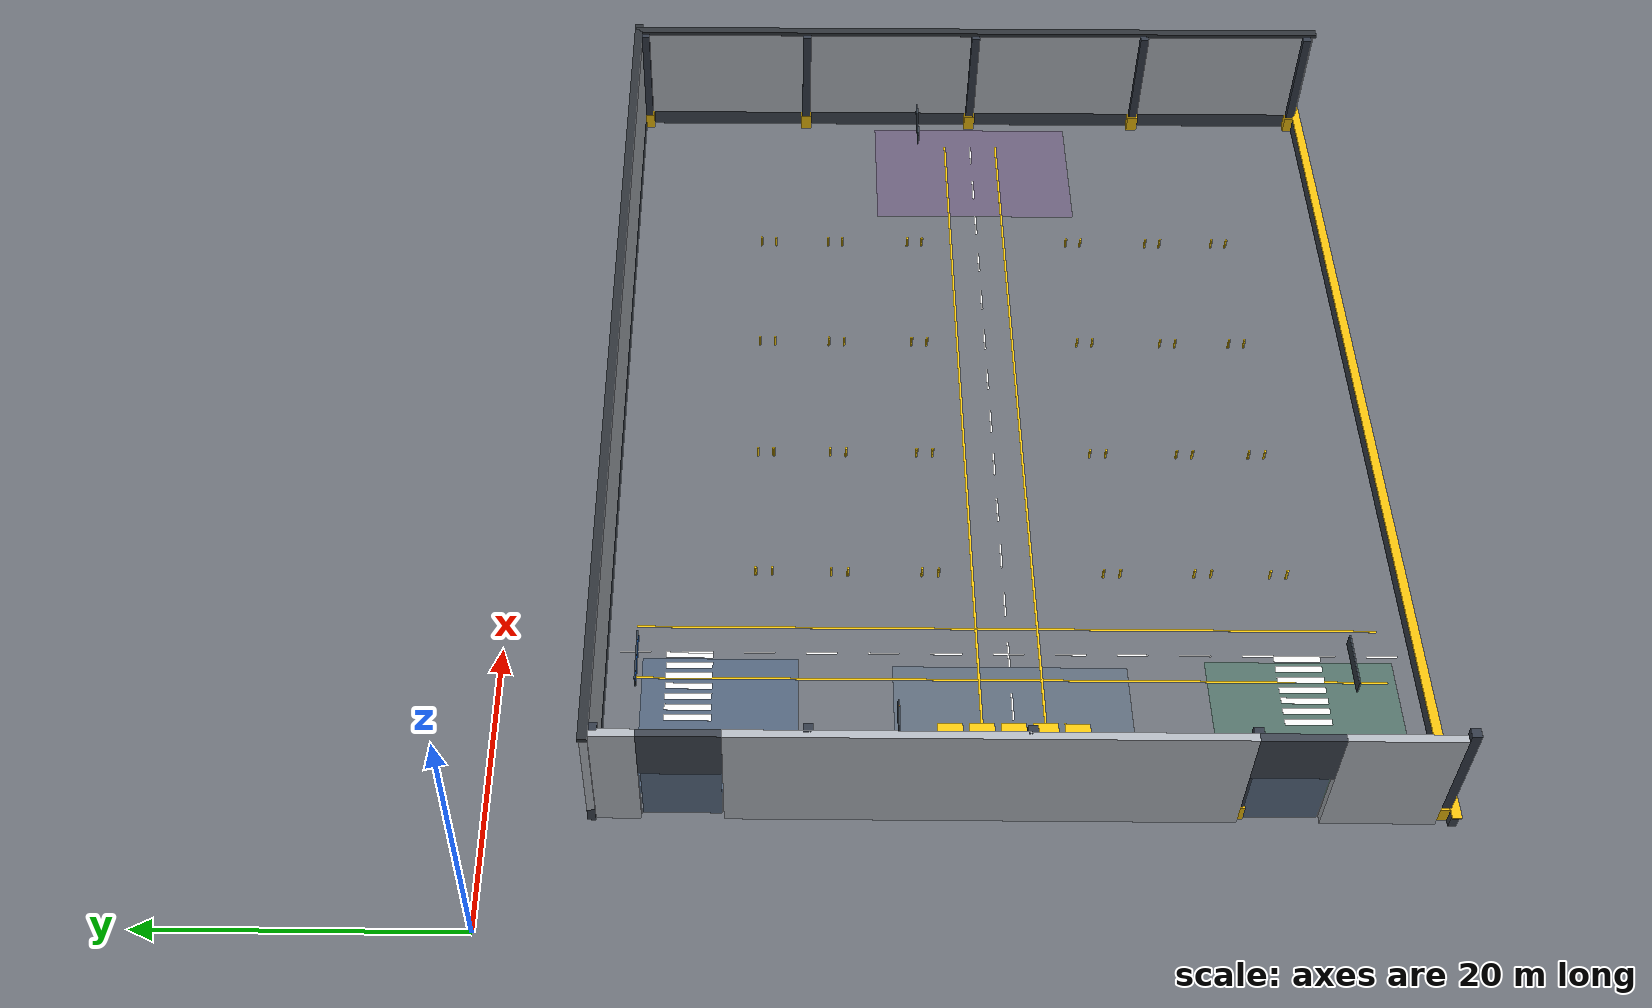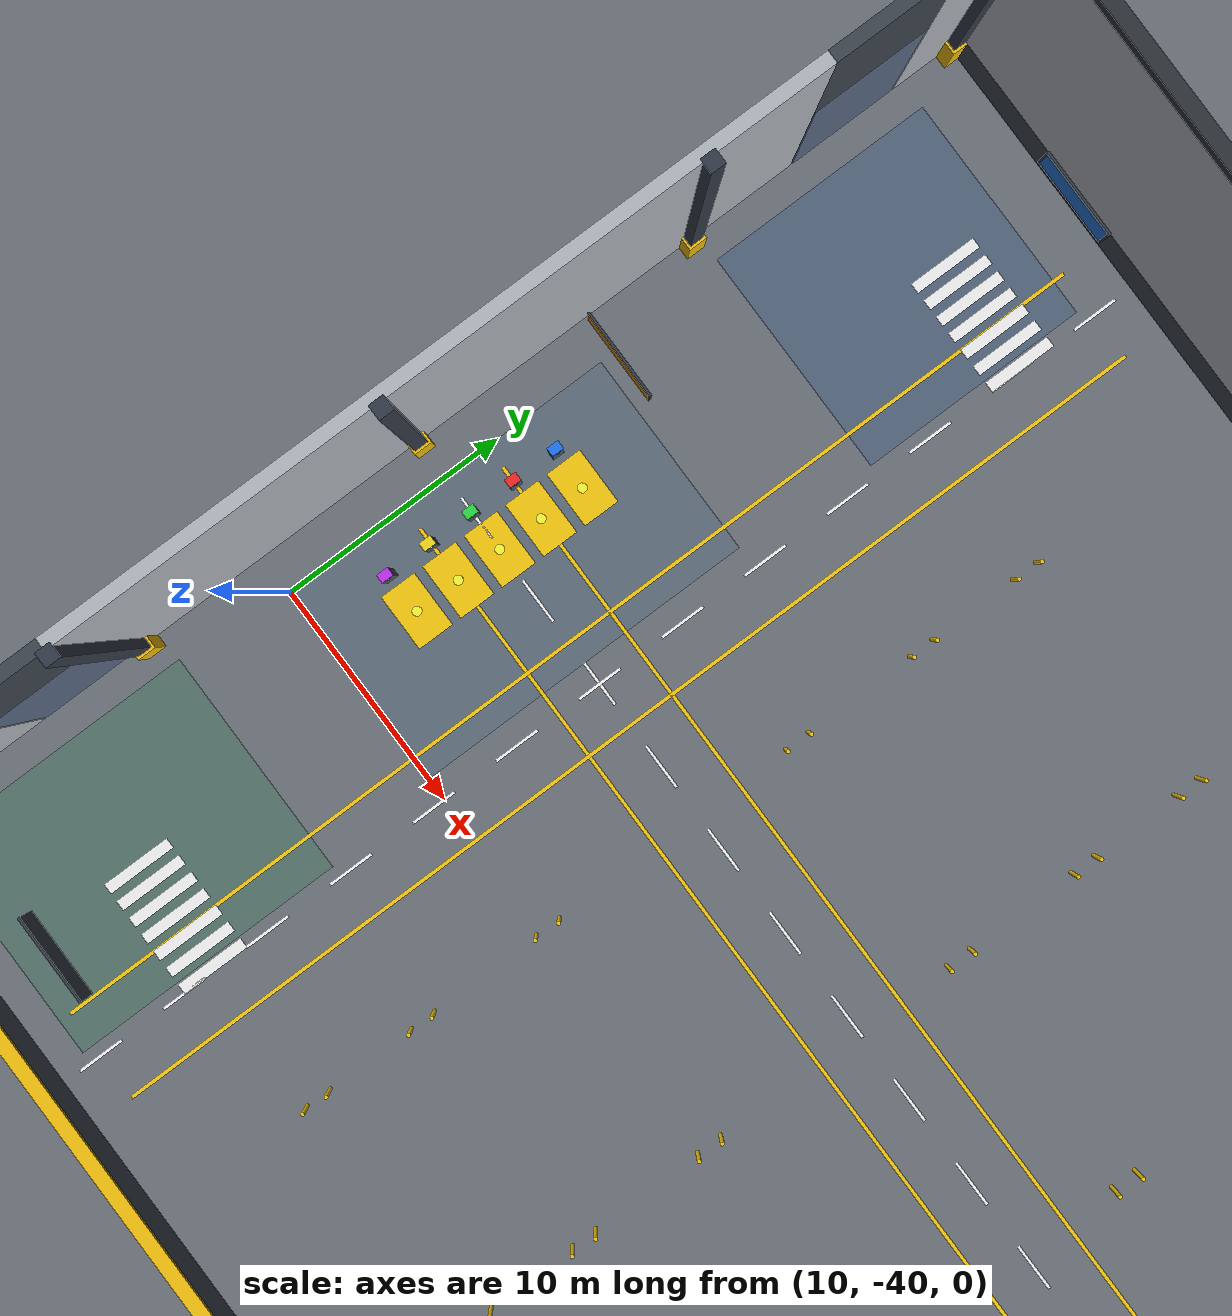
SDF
<sdf version="1.7">
 <world name="sim_world">
  <physics name="10ms" type="ode">
   <max_step_size>0.01</max_step_size>
   <real_time_factor>1.0</real_time_factor>
  </physics>
  <plugin filename="gz-sim-physics-system" name="gz::sim::systems::Physics"/>
  <plugin filename="gz-sim-user-commands-system" name="gz::sim::systems::UserCommands"/>
  <plugin filename="gz-sim-scene-broadcaster-system" name="gz::sim::systems::SceneBroadcaster"/>
  <plugin filename="gz-sim-sensors-system" name="gz::sim::systems::Sensors">
   <render_engine>ogre2</render_engine>
  </plugin>
  <plugin filename="gz-sim-imu-system" name="gz::sim::systems::Imu"/>
  <scene>
   <ambient>0.74 0.76 0.80 1.0</ambient>
   <background>0.16 0.18 0.22 1.0</background>
   <shadows>false</shadows>
   <grid>false</grid>
  </scene>
  <light type="directional" name="sun_primary">
   <cast_shadows>false</cast_shadows>
   <pose>40.0 -32.5 25.0 0 0 0</pose>
   <diffuse>0.88 0.88 0.92 1.0</diffuse>
   <specular>0.25 0.25 0.25 1.0</specular>
   <attenuation>
    <range>150</range>
    <constant>0.9</constant>
    <linear>0.01</linear>
    <quadratic>0.001</quadratic>
   </attenuation>
   <direction>-0.3 0.2 -0.9</direction>
  </light>
  <light type="point" name="bay_light_0">
   <pose>16.0 -14.0 9.0 0 0 0</pose>
   <diffuse>0.78 0.82 0.86 1.0</diffuse>
   <specular>0.20 0.20 0.25 1.0</specular>
   <attenuation>
    <range>28</range>
    <constant>0.22</constant>
    <linear>0.04</linear>
    <quadratic>0.005</quadratic>
   </attenuation>
   <cast_shadows>false</cast_shadows>
  </light>
  <light type="point" name="bay_light_1">
   <pose>16.0 -32.5 9.0 0 0 0</pose>
   <diffuse>0.78 0.82 0.86 1.0</diffuse>
   <specular>0.20 0.20 0.25 1.0</specular>
   <attenuation>
    <range>28</range>
    <constant>0.22</constant>
    <linear>0.04</linear>
    <quadratic>0.005</quadratic>
   </attenuation>
   <cast_shadows>false</cast_shadows>
  </light>
  <light type="point" name="bay_light_2">
   <pose>16.0 -50.0 9.0 0 0 0</pose>
   <diffuse>0.78 0.82 0.86 1.0</diffuse>
   <specular>0.20 0.20 0.25 1.0</specular>
   <attenuation>
    <range>28</range>
    <constant>0.22</constant>
    <linear>0.04</linear>
    <quadratic>0.005</quadratic>
   </attenuation>
   <cast_shadows>false</cast_shadows>
  </light>
  <light type="point" name="bay_light_3">
   <pose>30.0 -14.0 9.0 0 0 0</pose>
   <diffuse>0.78 0.82 0.86 1.0</diffuse>
   <specular>0.20 0.20 0.25 1.0</specular>
   <attenuation>
    <range>28</range>
    <constant>0.22</constant>
    <linear>0.04</linear>
    <quadratic>0.005</quadratic>
   </attenuation>
   <cast_shadows>false</cast_shadows>
  </light>
  <light type="point" name="bay_light_4">
   <pose>30.0 -32.5 9.0 0 0 0</pose>
   <diffuse>0.78 0.82 0.86 1.0</diffuse>
   <specular>0.20 0.20 0.25 1.0</specular>
   <attenuation>
    <range>28</range>
    <constant>0.22</constant>
    <linear>0.04</linear>
    <quadratic>0.005</quadratic>
   </attenuation>
   <cast_shadows>false</cast_shadows>
  </light>
  <light type="point" name="bay_light_5">
   <pose>30.0 -50.0 9.0 0 0 0</pose>
   <diffuse>0.78 0.82 0.86 1.0</diffuse>
   <specular>0.20 0.20 0.25 1.0</specular>
   <attenuation>
    <range>28</range>
    <constant>0.22</constant>
    <linear>0.04</linear>
    <quadratic>0.005</quadratic>
   </attenuation>
   <cast_shadows>false</cast_shadows>
  </light>
  <light type="point" name="bay_light_6">
   <pose>42.0 -14.0 9.0 0 0 0</pose>
   <diffuse>0.78 0.82 0.86 1.0</diffuse>
   <specular>0.20 0.20 0.25 1.0</specular>
   <attenuation>
    <range>28</range>
    <constant>0.22</constant>
    <linear>0.04</linear>
    <quadratic>0.005</quadratic>
   </attenuation>
   <cast_shadows>false</cast_shadows>
  </light>
  <light type="point" name="bay_light_7">
   <pose>42.0 -32.5 9.0 0 0 0</pose>
   <diffuse>0.78 0.82 0.86 1.0</diffuse>
   <specular>0.20 0.20 0.25 1.0</specular>
   <attenuation>
    <range>28</range>
    <constant>0.22</constant>
    <linear>0.04</linear>
    <quadratic>0.005</quadratic>
   </attenuation>
   <cast_shadows>false</cast_shadows>
  </light>
  <light type="point" name="bay_light_8">
   <pose>42.0 -50.0 9.0 0 0 0</pose>
   <diffuse>0.78 0.82 0.86 1.0</diffuse>
   <specular>0.20 0.20 0.25 1.0</specular>
   <attenuation>
    <range>28</range>
    <constant>0.22</constant>
    <linear>0.04</linear>
    <quadratic>0.005</quadratic>
   </attenuation>
   <cast_shadows>false</cast_shadows>
  </light>
  <light type="point" name="bay_light_9">
   <pose>54.0 -14.0 9.0 0 0 0</pose>
   <diffuse>0.78 0.82 0.86 1.0</diffuse>
   <specular>0.20 0.20 0.25 1.0</specular>
   <attenuation>
    <range>28</range>
    <constant>0.22</constant>
    <linear>0.04</linear>
    <quadratic>0.005</quadratic>
   </attenuation>
   <cast_shadows>false</cast_shadows>
  </light>
  <light type="point" name="bay_light_10">
   <pose>54.0 -32.5 9.0 0 0 0</pose>
   <diffuse>0.78 0.82 0.86 1.0</diffuse>
   <specular>0.20 0.20 0.25 1.0</specular>
   <attenuation>
    <range>28</range>
    <constant>0.22</constant>
    <linear>0.04</linear>
    <quadratic>0.005</quadratic>
   </attenuation>
   <cast_shadows>false</cast_shadows>
  </light>
  <light type="point" name="bay_light_11">
   <pose>54.0 -50.0 9.0 0 0 0</pose>
   <diffuse>0.78 0.82 0.86 1.0</diffuse>
   <specular>0.20 0.20 0.25 1.0</specular>
   <attenuation>
    <range>28</range>
    <constant>0.22</constant>
    <linear>0.04</linear>
    <quadratic>0.005</quadratic>
   </attenuation>
   <cast_shadows>false</cast_shadows>
  </light>
  <light type="point" name="bay_light_12">
   <pose>66.0 -14.0 9.0 0 0 0</pose>
   <diffuse>0.78 0.82 0.86 1.0</diffuse>
   <specular>0.20 0.20 0.25 1.0</specular>
   <attenuation>
    <range>28</range>
    <constant>0.22</constant>
    <linear>0.04</linear>
    <quadratic>0.005</quadratic>
   </attenuation>
   <cast_shadows>false</cast_shadows>
  </light>
  <light type="point" name="bay_light_13">
   <pose>66.0 -32.5 9.0 0 0 0</pose>
   <diffuse>0.78 0.82 0.86 1.0</diffuse>
   <specular>0.20 0.20 0.25 1.0</specular>
   <attenuation>
    <range>28</range>
    <constant>0.22</constant>
    <linear>0.04</linear>
    <quadratic>0.005</quadratic>
   </attenuation>
   <cast_shadows>false</cast_shadows>
  </light>
  <light type="point" name="bay_light_14">
   <pose>66.0 -50.0 9.0 0 0 0</pose>
   <diffuse>0.78 0.82 0.86 1.0</diffuse>
   <specular>0.20 0.20 0.25 1.0</specular>
   <attenuation>
    <range>28</range>
    <constant>0.22</constant>
    <linear>0.04</linear>
    <quadratic>0.005</quadratic>
   </attenuation>
   <cast_shadows>false</cast_shadows>
  </light>
  <model name="warehouse_floor">
   <static>true</static>
   <pose>40.0 -32.5 0.0 0 0 0</pose>
   <link name="floor_link">
    <collision name="floor_collision">
     <geometry><plane><normal>0 0 1</normal><size>76 62</size></plane></geometry>
     <surface><friction><ode><mu>1.0</mu><mu2>1.0</mu2></ode></friction></surface>
    </collision>
    <visual name="floor_visual">
     <geometry><plane><normal>0 0 1</normal><size>76 62</size></plane></geometry>
     <material>
      <ambient>0.34 0.36 0.38 1.0</ambient>
      <diffuse>0.42 0.44 0.47 1.0</diffuse>
      <specular>0.15 0.15 0.15 1.0</specular>
     </material>
    </visual>
   </link>
  </model>
  <model name="warehouse_architecture">
   <static>true</static>
   <pose>40.0 -32.5 0.0 0 0 0</pose>
   <link name="wall_north_base">
    <pose>0.0000 26.0000 0.6000 0.0000 0.0000 0.0000</pose>
    <collision name="wall_north_base_col">
     <geometry><box><size>64.8000 0.5000 1.2000</size></box></geometry>
    </collision>
    <visual name="wall_north_base_vis">
     <geometry><box><size>64.8000 0.5000 1.2000</size></box></geometry>
     <material>
      <ambient>0.156 0.176 0.202 1.00</ambient>
      <diffuse>0.240 0.270 0.310 1.00</diffuse>
      <specular>0.15 0.15 0.15 1.0</specular>
     </material>
    </visual>
   </link>
   <link name="wall_north_upper">
    <pose>0.0000 26.0000 5.0000 0.0000 0.0000 0.0000</pose>
    <collision name="wall_north_upper_col">
     <geometry><box><size>64.8000 0.5000 7.8000</size></box></geometry>
    </collision>
    <visual name="wall_north_upper_vis">
     <geometry><box><size>64.8000 0.5000 7.8000</size></box></geometry>
     <material>
      <ambient>0.455 0.468 0.488 1.00</ambient>
      <diffuse>0.700 0.720 0.750 1.00</diffuse>
      <specular>0.15 0.15 0.15 1.0</specular>
     </material>
    </visual>
   </link>
   <link name="wall_north_coping">
    <pose>0.0000 26.0000 9.0500 0.0000 0.0000 0.0000</pose>
    <visual name="wall_north_coping_vis">
     <geometry><box><size>65.2000 0.6000 0.3000</size></box></geometry>
     <material>
      <ambient>0.117 0.130 0.143 1.00</ambient>
      <diffuse>0.180 0.200 0.220 1.00</diffuse>
      <specular>0.15 0.15 0.15 1.0</specular>
     </material>
    </visual>
   </link>
   <link name="window_north">
    <pose>0.0000 25.8000 7.0000 0.0000 0.0000 0.0000</pose>
    <visual name="window_north_vis">
     <geometry><box><size>56.0000 0.0500 1.6000</size></box></geometry>
     <material>
      <ambient>0.293 0.423 0.552 0.70</ambient>
      <diffuse>0.450 0.650 0.850 0.70</diffuse>
      <specular>0.15 0.15 0.15 1.0</specular>
     </material>
    </visual>
   </link>
   <link name="wall_south_base">
    <pose>0.0000 -26.0000 0.6000 0.0000 0.0000 0.0000</pose>
    <collision name="wall_south_base_col">
     <geometry><box><size>64.8000 0.5000 1.2000</size></box></geometry>
    </collision>
    <visual name="wall_south_base_vis">
     <geometry><box><size>64.8000 0.5000 1.2000</size></box></geometry>
     <material>
      <ambient>0.156 0.176 0.202 1.00</ambient>
      <diffuse>0.240 0.270 0.310 1.00</diffuse>
      <specular>0.15 0.15 0.15 1.0</specular>
     </material>
    </visual>
   </link>
   <link name="wall_south_coping">
    <pose>0.0000 -26.0000 1.2500 0.0000 0.0000 0.0000</pose>
    <visual name="wall_south_coping_vis">
     <geometry><box><size>65.2000 0.6000 0.1000</size></box></geometry>
     <material>
      <ambient>0.617 0.488 0.033 1.00</ambient>
      <diffuse>0.950 0.750 0.050 1.00</diffuse>
      <specular>0.15 0.15 0.15 1.0</specular>
     </material>
    </visual>
   </link>
   <link name="wall_east_base">
    <pose>32.0000 0.0000 0.6000 0.0000 0.0000 0.0000</pose>
    <collision name="wall_east_base_col">
     <geometry><box><size>0.5000 52.0000 1.2000</size></box></geometry>
    </collision>
    <visual name="wall_east_base_vis">
     <geometry><box><size>0.5000 52.0000 1.2000</size></box></geometry>
     <material>
      <ambient>0.156 0.176 0.202 1.00</ambient>
      <diffuse>0.240 0.270 0.310 1.00</diffuse>
      <specular>0.15 0.15 0.15 1.0</specular>
     </material>
    </visual>
   </link>
   <link name="wall_east_upper">
    <pose>32.0000 0.0000 5.0000 0.0000 0.0000 0.0000</pose>
    <collision name="wall_east_upper_col">
     <geometry><box><size>0.5000 52.0000 7.8000</size></box></geometry>
    </collision>
    <visual name="wall_east_upper_vis">
     <geometry><box><size>0.5000 52.0000 7.8000</size></box></geometry>
     <material>
      <ambient>0.455 0.468 0.488 1.00</ambient>
      <diffuse>0.700 0.720 0.750 1.00</diffuse>
      <specular>0.15 0.15 0.15 1.0</specular>
     </material>
    </visual>
   </link>
   <link name="wall_east_coping">
    <pose>32.0000 0.0000 9.0500 0.0000 0.0000 0.0000</pose>
    <visual name="wall_east_coping_vis">
     <geometry><box><size>0.6000 52.4000 0.3000</size></box></geometry>
     <material>
      <ambient>0.117 0.130 0.143 1.00</ambient>
      <diffuse>0.180 0.200 0.220 1.00</diffuse>
      <specular>0.15 0.15 0.15 1.0</specular>
     </material>
    </visual>
   </link>
   <link name="window_east">
    <pose>31.8000 0.0000 7.0000 0.0000 0.0000 0.0000</pose>
    <visual name="window_east_vis">
     <geometry><box><size>0.0500 44.0000 1.6000</size></box></geometry>
     <material>
      <ambient>0.293 0.423 0.552 0.70</ambient>
      <diffuse>0.450 0.650 0.850 0.70</diffuse>
      <specular>0.15 0.15 0.15 1.0</specular>
     </material>
    </visual>
   </link>
   <link name="wall_west_n">
    <pose>-32.0000 24.5000 4.5000 0.0000 0.0000 0.0000</pose>
    <collision name="wall_west_n_col">
     <geometry><box><size>0.5000 3.0000 9.0000</size></box></geometry>
    </collision>
    <visual name="wall_west_n_vis">
     <geometry><box><size>0.5000 3.0000 9.0000</size></box></geometry>
     <material>
      <ambient>0.455 0.468 0.488 1.00</ambient>
      <diffuse>0.700 0.720 0.750 1.00</diffuse>
      <specular>0.15 0.15 0.15 1.0</specular>
     </material>
    </visual>
   </link>
   <link name="lintel_inbound">
    <pose>-32.0000 20.5000 7.0000 0.0000 0.0000 0.0000</pose>
    <collision name="lintel_inbound_col">
     <geometry><box><size>0.5000 5.0000 4.0000</size></box></geometry>
    </collision>
    <visual name="lintel_inbound_vis">
     <geometry><box><size>0.5000 5.0000 4.0000</size></box></geometry>
     <material>
      <ambient>0.156 0.176 0.202 1.00</ambient>
      <diffuse>0.240 0.270 0.310 1.00</diffuse>
      <specular>0.15 0.15 0.15 1.0</specular>
     </material>
    </visual>
   </link>
   <link name="shutter_inbound">
    <pose>-31.8000 20.5000 2.5000 0.0000 0.0000 0.0000</pose>
    <visual name="shutter_inbound_vis">
     <geometry><box><size>0.1000 4.8000 5.0000</size></box></geometry>
     <material>
      <ambient>0.227 0.273 0.338 1.00</ambient>
      <diffuse>0.350 0.420 0.520 1.00</diffuse>
      <specular>0.15 0.15 0.15 1.0</specular>
     </material>
    </visual>
   </link>
   <link name="wall_west_c">
    <pose>-32.0000 2.5000 4.5000 0.0000 0.0000 0.0000</pose>
    <collision name="wall_west_c_col">
     <geometry><box><size>0.5000 31.0000 9.0000</size></box></geometry>
    </collision>
    <visual name="wall_west_c_vis">
     <geometry><box><size>0.5000 31.0000 9.0000</size></box></geometry>
     <material>
      <ambient>0.455 0.468 0.488 1.00</ambient>
      <diffuse>0.700 0.720 0.750 1.00</diffuse>
      <specular>0.15 0.15 0.15 1.0</specular>
     </material>
    </visual>
   </link>
   <link name="lintel_outbound">
    <pose>-32.0000 -15.5000 7.0000 0.0000 0.0000 0.0000</pose>
    <collision name="lintel_outbound_col">
     <geometry><box><size>0.5000 5.0000 4.0000</size></box></geometry>
    </collision>
    <visual name="lintel_outbound_vis">
     <geometry><box><size>0.5000 5.0000 4.0000</size></box></geometry>
     <material>
      <ambient>0.156 0.176 0.202 1.00</ambient>
      <diffuse>0.240 0.270 0.310 1.00</diffuse>
      <specular>0.15 0.15 0.15 1.0</specular>
     </material>
    </visual>
   </link>
   <link name="shutter_outbound">
    <pose>-31.8000 -15.5000 2.5000 0.0000 0.0000 0.0000</pose>
    <visual name="shutter_outbound_vis">
     <geometry><box><size>0.1000 4.8000 5.0000</size></box></geometry>
     <material>
      <ambient>0.227 0.273 0.338 1.00</ambient>
      <diffuse>0.350 0.420 0.520 1.00</diffuse>
      <specular>0.15 0.15 0.15 1.0</specular>
     </material>
    </visual>
   </link>
   <link name="wall_west_s">
    <pose>-32.0000 -21.5000 4.5000 0.0000 0.0000 0.0000</pose>
    <collision name="wall_west_s_col">
     <geometry><box><size>0.5000 7.0000 9.0000</size></box></geometry>
    </collision>
    <visual name="wall_west_s_vis">
     <geometry><box><size>0.5000 7.0000 9.0000</size></box></geometry>
     <material>
      <ambient>0.455 0.468 0.488 1.00</ambient>
      <diffuse>0.700 0.720 0.750 1.00</diffuse>
      <specular>0.15 0.15 0.15 1.0</specular>
     </material>
    </visual>
   </link>
   <link name="pcol_-31.6_-25.5">
    <pose>-31.6000 -25.5000 4.5000 0.0000 0.0000 0.0000</pose>
    <collision name="pcol_-31.6_-25.5_col">
     <geometry><box><size>0.6000 0.6000 9.0000</size></box></geometry>
    </collision>
    <visual name="pcol_-31.6_-25.5_vis">
     <geometry><box><size>0.6000 0.6000 9.0000</size></box></geometry>
     <material>
      <ambient>0.130 0.150 0.182 1.00</ambient>
      <diffuse>0.200 0.230 0.280 1.00</diffuse>
      <specular>0.15 0.15 0.15 1.0</specular>
     </material>
    </visual>
   </link>
   <link name="pcol_base_-31.6_-25.5">
    <pose>-31.6000 -25.5000 0.6000 0.0000 0.0000 0.0000</pose>
    <visual name="pcol_base_-31.6_-25.5_vis">
     <geometry><box><size>0.8000 0.8000 1.2000</size></box></geometry>
     <material>
      <ambient>0.617 0.488 0.033 1.00</ambient>
      <diffuse>0.950 0.750 0.050 1.00</diffuse>
      <specular>0.15 0.15 0.15 1.0</specular>
     </material>
    </visual>
   </link>
   <link name="pcol_-31.6_-13.0">
    <pose>-31.6000 -13.0000 4.5000 0.0000 0.0000 0.0000</pose>
    <collision name="pcol_-31.6_-13.0_col">
     <geometry><box><size>0.6000 0.6000 9.0000</size></box></geometry>
    </collision>
    <visual name="pcol_-31.6_-13.0_vis">
     <geometry><box><size>0.6000 0.6000 9.0000</size></box></geometry>
     <material>
      <ambient>0.130 0.150 0.182 1.00</ambient>
      <diffuse>0.200 0.230 0.280 1.00</diffuse>
      <specular>0.15 0.15 0.15 1.0</specular>
     </material>
    </visual>
   </link>
   <link name="pcol_base_-31.6_-13.0">
    <pose>-31.6000 -13.0000 0.6000 0.0000 0.0000 0.0000</pose>
    <visual name="pcol_base_-31.6_-13.0_vis">
     <geometry><box><size>0.8000 0.8000 1.2000</size></box></geometry>
     <material>
      <ambient>0.617 0.488 0.033 1.00</ambient>
      <diffuse>0.950 0.750 0.050 1.00</diffuse>
      <specular>0.15 0.15 0.15 1.0</specular>
     </material>
    </visual>
   </link>
   <link name="pcol_-31.6_0.0">
    <pose>-31.6000 0.0000 4.5000 0.0000 0.0000 0.0000</pose>
    <collision name="pcol_-31.6_0.0_col">
     <geometry><box><size>0.6000 0.6000 9.0000</size></box></geometry>
    </collision>
    <visual name="pcol_-31.6_0.0_vis">
     <geometry><box><size>0.6000 0.6000 9.0000</size></box></geometry>
     <material>
      <ambient>0.130 0.150 0.182 1.00</ambient>
      <diffuse>0.200 0.230 0.280 1.00</diffuse>
      <specular>0.15 0.15 0.15 1.0</specular>
     </material>
    </visual>
   </link>
   <link name="pcol_base_-31.6_0.0">
    <pose>-31.6000 0.0000 0.6000 0.0000 0.0000 0.0000</pose>
    <visual name="pcol_base_-31.6_0.0_vis">
     <geometry><box><size>0.8000 0.8000 1.2000</size></box></geometry>
     <material>
      <ambient>0.617 0.488 0.033 1.00</ambient>
      <diffuse>0.950 0.750 0.050 1.00</diffuse>
      <specular>0.15 0.15 0.15 1.0</specular>
     </material>
    </visual>
   </link>
   <link name="pcol_-31.6_13.0">
    <pose>-31.6000 13.0000 4.5000 0.0000 0.0000 0.0000</pose>
    <collision name="pcol_-31.6_13.0_col">
     <geometry><box><size>0.6000 0.6000 9.0000</size></box></geometry>
    </collision>
    <visual name="pcol_-31.6_13.0_vis">
     <geometry><box><size>0.6000 0.6000 9.0000</size></box></geometry>
     <material>
      <ambient>0.130 0.150 0.182 1.00</ambient>
      <diffuse>0.200 0.230 0.280 1.00</diffuse>
      <specular>0.15 0.15 0.15 1.0</specular>
     </material>
    </visual>
   </link>
   <link name="pcol_base_-31.6_13.0">
    <pose>-31.6000 13.0000 0.6000 0.0000 0.0000 0.0000</pose>
    <visual name="pcol_base_-31.6_13.0_vis">
     <geometry><box><size>0.8000 0.8000 1.2000</size></box></geometry>
     <material>
      <ambient>0.617 0.488 0.033 1.00</ambient>
      <diffuse>0.950 0.750 0.050 1.00</diffuse>
      <specular>0.15 0.15 0.15 1.0</specular>
     </material>
    </visual>
   </link>
   <link name="pcol_-31.6_25.5">
    <pose>-31.6000 25.5000 4.5000 0.0000 0.0000 0.0000</pose>
    <collision name="pcol_-31.6_25.5_col">
     <geometry><box><size>0.6000 0.6000 9.0000</size></box></geometry>
    </collision>
    <visual name="pcol_-31.6_25.5_vis">
     <geometry><box><size>0.6000 0.6000 9.0000</size></box></geometry>
     <material>
      <ambient>0.130 0.150 0.182 1.00</ambient>
      <diffuse>0.200 0.230 0.280 1.00</diffuse>
      <specular>0.15 0.15 0.15 1.0</specular>
     </material>
    </visual>
   </link>
   <link name="pcol_base_-31.6_25.5">
    <pose>-31.6000 25.5000 0.6000 0.0000 0.0000 0.0000</pose>
    <visual name="pcol_base_-31.6_25.5_vis">
     <geometry><box><size>0.8000 0.8000 1.2000</size></box></geometry>
     <material>
      <ambient>0.617 0.488 0.033 1.00</ambient>
      <diffuse>0.950 0.750 0.050 1.00</diffuse>
      <specular>0.15 0.15 0.15 1.0</specular>
     </material>
    </visual>
   </link>
   <link name="pcol_31.6_-25.5">
    <pose>31.6000 -25.5000 4.5000 0.0000 0.0000 0.0000</pose>
    <collision name="pcol_31.6_-25.5_col">
     <geometry><box><size>0.6000 0.6000 9.0000</size></box></geometry>
    </collision>
    <visual name="pcol_31.6_-25.5_vis">
     <geometry><box><size>0.6000 0.6000 9.0000</size></box></geometry>
     <material>
      <ambient>0.130 0.150 0.182 1.00</ambient>
      <diffuse>0.200 0.230 0.280 1.00</diffuse>
      <specular>0.15 0.15 0.15 1.0</specular>
     </material>
    </visual>
   </link>
   <link name="pcol_base_31.6_-25.5">
    <pose>31.6000 -25.5000 0.6000 0.0000 0.0000 0.0000</pose>
    <visual name="pcol_base_31.6_-25.5_vis">
     <geometry><box><size>0.8000 0.8000 1.2000</size></box></geometry>
     <material>
      <ambient>0.617 0.488 0.033 1.00</ambient>
      <diffuse>0.950 0.750 0.050 1.00</diffuse>
      <specular>0.15 0.15 0.15 1.0</specular>
     </material>
    </visual>
   </link>
   <link name="pcol_31.6_-13.0">
    <pose>31.6000 -13.0000 4.5000 0.0000 0.0000 0.0000</pose>
    <collision name="pcol_31.6_-13.0_col">
     <geometry><box><size>0.6000 0.6000 9.0000</size></box></geometry>
    </collision>
    <visual name="pcol_31.6_-13.0_vis">
     <geometry><box><size>0.6000 0.6000 9.0000</size></box></geometry>
     <material>
      <ambient>0.130 0.150 0.182 1.00</ambient>
      <diffuse>0.200 0.230 0.280 1.00</diffuse>
      <specular>0.15 0.15 0.15 1.0</specular>
     </material>
    </visual>
   </link>
   <link name="pcol_base_31.6_-13.0">
    <pose>31.6000 -13.0000 0.6000 0.0000 0.0000 0.0000</pose>
    <visual name="pcol_base_31.6_-13.0_vis">
     <geometry><box><size>0.8000 0.8000 1.2000</size></box></geometry>
     <material>
      <ambient>0.617 0.488 0.033 1.00</ambient>
      <diffuse>0.950 0.750 0.050 1.00</diffuse>
      <specular>0.15 0.15 0.15 1.0</specular>
     </material>
    </visual>
   </link>
   <link name="pcol_31.6_0.0">
    <pose>31.6000 0.0000 4.5000 0.0000 0.0000 0.0000</pose>
    <collision name="pcol_31.6_0.0_col">
     <geometry><box><size>0.6000 0.6000 9.0000</size></box></geometry>
    </collision>
    <visual name="pcol_31.6_0.0_vis">
     <geometry><box><size>0.6000 0.6000 9.0000</size></box></geometry>
     <material>
      <ambient>0.130 0.150 0.182 1.00</ambient>
      <diffuse>0.200 0.230 0.280 1.00</diffuse>
      <specular>0.15 0.15 0.15 1.0</specular>
     </material>
    </visual>
   </link>
   <link name="pcol_base_31.6_0.0">
    <pose>31.6000 0.0000 0.6000 0.0000 0.0000 0.0000</pose>
    <visual name="pcol_base_31.6_0.0_vis">
     <geometry><box><size>0.8000 0.8000 1.2000</size></box></geometry>
     <material>
      <ambient>0.617 0.488 0.033 1.00</ambient>
      <diffuse>0.950 0.750 0.050 1.00</diffuse>
      <specular>0.15 0.15 0.15 1.0</specular>
     </material>
    </visual>
   </link>
   <link name="pcol_31.6_13.0">
    <pose>31.6000 13.0000 4.5000 0.0000 0.0000 0.0000</pose>
    <collision name="pcol_31.6_13.0_col">
     <geometry><box><size>0.6000 0.6000 9.0000</size></box></geometry>
    </collision>
    <visual name="pcol_31.6_13.0_vis">
     <geometry><box><size>0.6000 0.6000 9.0000</size></box></geometry>
     <material>
      <ambient>0.130 0.150 0.182 1.00</ambient>
      <diffuse>0.200 0.230 0.280 1.00</diffuse>
      <specular>0.15 0.15 0.15 1.0</specular>
     </material>
    </visual>
   </link>
   <link name="pcol_base_31.6_13.0">
    <pose>31.6000 13.0000 0.6000 0.0000 0.0000 0.0000</pose>
    <visual name="pcol_base_31.6_13.0_vis">
     <geometry><box><size>0.8000 0.8000 1.2000</size></box></geometry>
     <material>
      <ambient>0.617 0.488 0.033 1.00</ambient>
      <diffuse>0.950 0.750 0.050 1.00</diffuse>
      <specular>0.15 0.15 0.15 1.0</specular>
     </material>
    </visual>
   </link>
   <link name="pcol_31.6_25.5">
    <pose>31.6000 25.5000 4.5000 0.0000 0.0000 0.0000</pose>
    <collision name="pcol_31.6_25.5_col">
     <geometry><box><size>0.6000 0.6000 9.0000</size></box></geometry>
    </collision>
    <visual name="pcol_31.6_25.5_vis">
     <geometry><box><size>0.6000 0.6000 9.0000</size></box></geometry>
     <material>
      <ambient>0.130 0.150 0.182 1.00</ambient>
      <diffuse>0.200 0.230 0.280 1.00</diffuse>
      <specular>0.15 0.15 0.15 1.0</specular>
     </material>
    </visual>
   </link>
   <link name="pcol_base_31.6_25.5">
    <pose>31.6000 25.5000 0.6000 0.0000 0.0000 0.0000</pose>
    <visual name="pcol_base_31.6_25.5_vis">
     <geometry><box><size>0.8000 0.8000 1.2000</size></box></geometry>
     <material>
      <ambient>0.617 0.488 0.033 1.00</ambient>
      <diffuse>0.950 0.750 0.050 1.00</diffuse>
      <specular>0.15 0.15 0.15 1.0</specular>
     </material>
    </visual>
   </link>
  </model>
  <model name="industrial_floor_markings">
   <static>true</static>
   <pose>40.0 -32.5 0.0 0 0 0</pose>
   <link name="highway_line_w">
    <pose>-22.0000 0.0000 0.0020 0.0000 0.0000 0.0000</pose>
    <visual name="highway_line_w_vis">
     <geometry><box><size>0.1500 48.0000 0.0010</size></box></geometry>
     <material>
      <ambient>0.624 0.507 0.033 1.00</ambient>
      <diffuse>0.960 0.780 0.050 1.00</diffuse>
      <specular>0.15 0.15 0.15 1.0</specular>
     </material>
    </visual>
   </link>
   <link name="highway_line_e">
    <pose>-18.0000 0.0000 0.0020 0.0000 0.0000 0.0000</pose>
    <visual name="highway_line_e_vis">
     <geometry><box><size>0.1500 48.0000 0.0010</size></box></geometry>
     <material>
      <ambient>0.624 0.507 0.033 1.00</ambient>
      <diffuse>0.960 0.780 0.050 1.00</diffuse>
      <specular>0.15 0.15 0.15 1.0</specular>
     </material>
    </visual>
   </link>
   <link name="highway_dash_0">
    <pose>-20.0000 -24.0000 0.0030 0.0000 0.0000 0.0000</pose>
    <visual name="highway_dash_0_vis">
     <geometry><box><size>0.1200 2.0000 0.0010</size></box></geometry>
     <material>
      <ambient>0.624 0.624 0.624 1.00</ambient>
      <diffuse>0.960 0.960 0.960 1.00</diffuse>
      <specular>0.15 0.15 0.15 1.0</specular>
     </material>
    </visual>
   </link>
   <link name="highway_dash_1">
    <pose>-20.0000 -20.0000 0.0030 0.0000 0.0000 0.0000</pose>
    <visual name="highway_dash_1_vis">
     <geometry><box><size>0.1200 2.0000 0.0010</size></box></geometry>
     <material>
      <ambient>0.624 0.624 0.624 1.00</ambient>
      <diffuse>0.960 0.960 0.960 1.00</diffuse>
      <specular>0.15 0.15 0.15 1.0</specular>
     </material>
    </visual>
   </link>
   <link name="highway_dash_2">
    <pose>-20.0000 -16.0000 0.0030 0.0000 0.0000 0.0000</pose>
    <visual name="highway_dash_2_vis">
     <geometry><box><size>0.1200 2.0000 0.0010</size></box></geometry>
     <material>
      <ambient>0.624 0.624 0.624 1.00</ambient>
      <diffuse>0.960 0.960 0.960 1.00</diffuse>
      <specular>0.15 0.15 0.15 1.0</specular>
     </material>
    </visual>
   </link>
   <link name="highway_dash_3">
    <pose>-20.0000 -12.0000 0.0030 0.0000 0.0000 0.0000</pose>
    <visual name="highway_dash_3_vis">
     <geometry><box><size>0.1200 2.0000 0.0010</size></box></geometry>
     <material>
      <ambient>0.624 0.624 0.624 1.00</ambient>
      <diffuse>0.960 0.960 0.960 1.00</diffuse>
      <specular>0.15 0.15 0.15 1.0</specular>
     </material>
    </visual>
   </link>
   <link name="highway_dash_4">
    <pose>-20.0000 -8.0000 0.0030 0.0000 0.0000 0.0000</pose>
    <visual name="highway_dash_4_vis">
     <geometry><box><size>0.1200 2.0000 0.0010</size></box></geometry>
     <material>
      <ambient>0.624 0.624 0.624 1.00</ambient>
      <diffuse>0.960 0.960 0.960 1.00</diffuse>
      <specular>0.15 0.15 0.15 1.0</specular>
     </material>
    </visual>
   </link>
   <link name="highway_dash_5">
    <pose>-20.0000 -4.0000 0.0030 0.0000 0.0000 0.0000</pose>
    <visual name="highway_dash_5_vis">
     <geometry><box><size>0.1200 2.0000 0.0010</size></box></geometry>
     <material>
      <ambient>0.624 0.624 0.624 1.00</ambient>
      <diffuse>0.960 0.960 0.960 1.00</diffuse>
      <specular>0.15 0.15 0.15 1.0</specular>
     </material>
    </visual>
   </link>
   <link name="highway_dash_6">
    <pose>-20.0000 0.0000 0.0030 0.0000 0.0000 0.0000</pose>
    <visual name="highway_dash_6_vis">
     <geometry><box><size>0.1200 2.0000 0.0010</size></box></geometry>
     <material>
      <ambient>0.624 0.624 0.624 1.00</ambient>
      <diffuse>0.960 0.960 0.960 1.00</diffuse>
      <specular>0.15 0.15 0.15 1.0</specular>
     </material>
    </visual>
   </link>
   <link name="highway_dash_7">
    <pose>-20.0000 4.0000 0.0030 0.0000 0.0000 0.0000</pose>
    <visual name="highway_dash_7_vis">
     <geometry><box><size>0.1200 2.0000 0.0010</size></box></geometry>
     <material>
      <ambient>0.624 0.624 0.624 1.00</ambient>
      <diffuse>0.960 0.960 0.960 1.00</diffuse>
      <specular>0.15 0.15 0.15 1.0</specular>
     </material>
    </visual>
   </link>
   <link name="highway_dash_8">
    <pose>-20.0000 8.0000 0.0030 0.0000 0.0000 0.0000</pose>
    <visual name="highway_dash_8_vis">
     <geometry><box><size>0.1200 2.0000 0.0010</size></box></geometry>
     <material>
      <ambient>0.624 0.624 0.624 1.00</ambient>
      <diffuse>0.960 0.960 0.960 1.00</diffuse>
      <specular>0.15 0.15 0.15 1.0</specular>
     </material>
    </visual>
   </link>
   <link name="highway_dash_9">
    <pose>-20.0000 12.0000 0.0030 0.0000 0.0000 0.0000</pose>
    <visual name="highway_dash_9_vis">
     <geometry><box><size>0.1200 2.0000 0.0010</size></box></geometry>
     <material>
      <ambient>0.624 0.624 0.624 1.00</ambient>
      <diffuse>0.960 0.960 0.960 1.00</diffuse>
      <specular>0.15 0.15 0.15 1.0</specular>
     </material>
    </visual>
   </link>
   <link name="highway_dash_10">
    <pose>-20.0000 16.0000 0.0030 0.0000 0.0000 0.0000</pose>
    <visual name="highway_dash_10_vis">
     <geometry><box><size>0.1200 2.0000 0.0010</size></box></geometry>
     <material>
      <ambient>0.624 0.624 0.624 1.00</ambient>
      <diffuse>0.960 0.960 0.960 1.00</diffuse>
      <specular>0.15 0.15 0.15 1.0</specular>
     </material>
    </visual>
   </link>
   <link name="highway_dash_11">
    <pose>-20.0000 20.0000 0.0030 0.0000 0.0000 0.0000</pose>
    <visual name="highway_dash_11_vis">
     <geometry><box><size>0.1200 2.0000 0.0010</size></box></geometry>
     <material>
      <ambient>0.624 0.624 0.624 1.00</ambient>
      <diffuse>0.960 0.960 0.960 1.00</diffuse>
      <specular>0.15 0.15 0.15 1.0</specular>
     </material>
    </visual>
   </link>
   <link name="highway_dash_12">
    <pose>-20.0000 24.0000 0.0030 0.0000 0.0000 0.0000</pose>
    <visual name="highway_dash_12_vis">
     <geometry><box><size>0.1200 2.0000 0.0010</size></box></geometry>
     <material>
      <ambient>0.624 0.624 0.624 1.00</ambient>
      <diffuse>0.960 0.960 0.960 1.00</diffuse>
      <specular>0.15 0.15 0.15 1.0</specular>
     </material>
    </visual>
   </link>
   <link name="cross_line_s">
    <pose>0.0000 -2.0000 0.0020 0.0000 0.0000 0.0000</pose>
    <visual name="cross_line_s_vis">
     <geometry><box><size>58.0000 0.1500 0.0010</size></box></geometry>
     <material>
      <ambient>0.624 0.507 0.033 1.00</ambient>
      <diffuse>0.960 0.780 0.050 1.00</diffuse>
      <specular>0.15 0.15 0.15 1.0</specular>
     </material>
    </visual>
   </link>
   <link name="cross_line_n">
    <pose>0.0000 2.0000 0.0020 0.0000 0.0000 0.0000</pose>
    <visual name="cross_line_n_vis">
     <geometry><box><size>58.0000 0.1500 0.0010</size></box></geometry>
     <material>
      <ambient>0.624 0.507 0.033 1.00</ambient>
      <diffuse>0.960 0.780 0.050 1.00</diffuse>
      <specular>0.15 0.15 0.15 1.0</specular>
     </material>
    </visual>
   </link>
   <link name="cross_dash_0">
    <pose>-28.0000 0.0000 0.0030 0.0000 0.0000 0.0000</pose>
    <visual name="cross_dash_0_vis">
     <geometry><box><size>2.0000 0.1200 0.0010</size></box></geometry>
     <material>
      <ambient>0.624 0.624 0.624 1.00</ambient>
      <diffuse>0.960 0.960 0.960 1.00</diffuse>
      <specular>0.15 0.15 0.15 1.0</specular>
     </material>
    </visual>
   </link>
   <link name="cross_dash_1">
    <pose>-24.0000 0.0000 0.0030 0.0000 0.0000 0.0000</pose>
    <visual name="cross_dash_1_vis">
     <geometry><box><size>2.0000 0.1200 0.0010</size></box></geometry>
     <material>
      <ambient>0.624 0.624 0.624 1.00</ambient>
      <diffuse>0.960 0.960 0.960 1.00</diffuse>
      <specular>0.15 0.15 0.15 1.0</specular>
     </material>
    </visual>
   </link>
   <link name="cross_dash_2">
    <pose>-20.0000 0.0000 0.0030 0.0000 0.0000 0.0000</pose>
    <visual name="cross_dash_2_vis">
     <geometry><box><size>2.0000 0.1200 0.0010</size></box></geometry>
     <material>
      <ambient>0.624 0.624 0.624 1.00</ambient>
      <diffuse>0.960 0.960 0.960 1.00</diffuse>
      <specular>0.15 0.15 0.15 1.0</specular>
     </material>
    </visual>
   </link>
   <link name="cross_dash_3">
    <pose>-16.0000 0.0000 0.0030 0.0000 0.0000 0.0000</pose>
    <visual name="cross_dash_3_vis">
     <geometry><box><size>2.0000 0.1200 0.0010</size></box></geometry>
     <material>
      <ambient>0.624 0.624 0.624 1.00</ambient>
      <diffuse>0.960 0.960 0.960 1.00</diffuse>
      <specular>0.15 0.15 0.15 1.0</specular>
     </material>
    </visual>
   </link>
   <link name="cross_dash_4">
    <pose>-12.0000 0.0000 0.0030 0.0000 0.0000 0.0000</pose>
    <visual name="cross_dash_4_vis">
     <geometry><box><size>2.0000 0.1200 0.0010</size></box></geometry>
     <material>
      <ambient>0.624 0.624 0.624 1.00</ambient>
      <diffuse>0.960 0.960 0.960 1.00</diffuse>
      <specular>0.15 0.15 0.15 1.0</specular>
     </material>
    </visual>
   </link>
   <link name="cross_dash_5">
    <pose>-8.0000 0.0000 0.0030 0.0000 0.0000 0.0000</pose>
    <visual name="cross_dash_5_vis">
     <geometry><box><size>2.0000 0.1200 0.0010</size></box></geometry>
     <material>
      <ambient>0.624 0.624 0.624 1.00</ambient>
      <diffuse>0.960 0.960 0.960 1.00</diffuse>
      <specular>0.15 0.15 0.15 1.0</specular>
     </material>
    </visual>
   </link>
   <link name="cross_dash_6">
    <pose>-4.0000 0.0000 0.0030 0.0000 0.0000 0.0000</pose>
    <visual name="cross_dash_6_vis">
     <geometry><box><size>2.0000 0.1200 0.0010</size></box></geometry>
     <material>
      <ambient>0.624 0.624 0.624 1.00</ambient>
      <diffuse>0.960 0.960 0.960 1.00</diffuse>
      <specular>0.15 0.15 0.15 1.0</specular>
     </material>
    </visual>
   </link>
   <link name="cross_dash_7">
    <pose>0.0000 0.0000 0.0030 0.0000 0.0000 0.0000</pose>
    <visual name="cross_dash_7_vis">
     <geometry><box><size>2.0000 0.1200 0.0010</size></box></geometry>
     <material>
      <ambient>0.624 0.624 0.624 1.00</ambient>
      <diffuse>0.960 0.960 0.960 1.00</diffuse>
      <specular>0.15 0.15 0.15 1.0</specular>
     </material>
    </visual>
   </link>
   <link name="cross_dash_8">
    <pose>4.0000 0.0000 0.0030 0.0000 0.0000 0.0000</pose>
    <visual name="cross_dash_8_vis">
     <geometry><box><size>2.0000 0.1200 0.0010</size></box></geometry>
     <material>
      <ambient>0.624 0.624 0.624 1.00</ambient>
      <diffuse>0.960 0.960 0.960 1.00</diffuse>
      <specular>0.15 0.15 0.15 1.0</specular>
     </material>
    </visual>
   </link>
   <link name="cross_dash_9">
    <pose>8.0000 0.0000 0.0030 0.0000 0.0000 0.0000</pose>
    <visual name="cross_dash_9_vis">
     <geometry><box><size>2.0000 0.1200 0.0010</size></box></geometry>
     <material>
      <ambient>0.624 0.624 0.624 1.00</ambient>
      <diffuse>0.960 0.960 0.960 1.00</diffuse>
      <specular>0.15 0.15 0.15 1.0</specular>
     </material>
    </visual>
   </link>
   <link name="cross_dash_10">
    <pose>12.0000 0.0000 0.0030 0.0000 0.0000 0.0000</pose>
    <visual name="cross_dash_10_vis">
     <geometry><box><size>2.0000 0.1200 0.0010</size></box></geometry>
     <material>
      <ambient>0.624 0.624 0.624 1.00</ambient>
      <diffuse>0.960 0.960 0.960 1.00</diffuse>
      <specular>0.15 0.15 0.15 1.0</specular>
     </material>
    </visual>
   </link>
   <link name="cross_dash_11">
    <pose>16.0000 0.0000 0.0030 0.0000 0.0000 0.0000</pose>
    <visual name="cross_dash_11_vis">
     <geometry><box><size>2.0000 0.1200 0.0010</size></box></geometry>
     <material>
      <ambient>0.624 0.624 0.624 1.00</ambient>
      <diffuse>0.960 0.960 0.960 1.00</diffuse>
      <specular>0.15 0.15 0.15 1.0</specular>
     </material>
    </visual>
   </link>
   <link name="cross_dash_12">
    <pose>20.0000 0.0000 0.0030 0.0000 0.0000 0.0000</pose>
    <visual name="cross_dash_12_vis">
     <geometry><box><size>2.0000 0.1200 0.0010</size></box></geometry>
     <material>
      <ambient>0.624 0.624 0.624 1.00</ambient>
      <diffuse>0.960 0.960 0.960 1.00</diffuse>
      <specular>0.15 0.15 0.15 1.0</specular>
     </material>
    </visual>
   </link>
   <link name="cross_dash_13">
    <pose>24.0000 0.0000 0.0030 0.0000 0.0000 0.0000</pose>
    <visual name="cross_dash_13_vis">
     <geometry><box><size>2.0000 0.1200 0.0010</size></box></geometry>
     <material>
      <ambient>0.624 0.624 0.624 1.00</ambient>
      <diffuse>0.960 0.960 0.960 1.00</diffuse>
      <specular>0.15 0.15 0.15 1.0</specular>
     </material>
    </visual>
   </link>
   <link name="cross_dash_14">
    <pose>28.0000 0.0000 0.0030 0.0000 0.0000 0.0000</pose>
    <visual name="cross_dash_14_vis">
     <geometry><box><size>2.0000 0.1200 0.0010</size></box></geometry>
     <material>
      <ambient>0.624 0.624 0.624 1.00</ambient>
      <diffuse>0.960 0.960 0.960 1.00</diffuse>
      <specular>0.15 0.15 0.15 1.0</specular>
     </material>
    </visual>
   </link>
   <link name="zebra_in_0">
    <pose>-25.0000 20.5000 0.0030 0.0000 0.0000 0.0000</pose>
    <visual name="zebra_in_0_vis">
     <geometry><box><size>0.4500 3.0000 0.0010</size></box></geometry>
     <material>
      <ambient>0.617 0.617 0.617 1.00</ambient>
      <diffuse>0.950 0.950 0.950 1.00</diffuse>
      <specular>0.15 0.15 0.15 1.0</specular>
     </material>
    </visual>
   </link>
   <link name="zebra_in_1">
    <pose>-24.2000 20.5000 0.0030 0.0000 0.0000 0.0000</pose>
    <visual name="zebra_in_1_vis">
     <geometry><box><size>0.4500 3.0000 0.0010</size></box></geometry>
     <material>
      <ambient>0.617 0.617 0.617 1.00</ambient>
      <diffuse>0.950 0.950 0.950 1.00</diffuse>
      <specular>0.15 0.15 0.15 1.0</specular>
     </material>
    </visual>
   </link>
   <link name="zebra_in_2">
    <pose>-23.4000 20.5000 0.0030 0.0000 0.0000 0.0000</pose>
    <visual name="zebra_in_2_vis">
     <geometry><box><size>0.4500 3.0000 0.0010</size></box></geometry>
     <material>
      <ambient>0.617 0.617 0.617 1.00</ambient>
      <diffuse>0.950 0.950 0.950 1.00</diffuse>
      <specular>0.15 0.15 0.15 1.0</specular>
     </material>
    </visual>
   </link>
   <link name="zebra_in_3">
    <pose>-22.6000 20.5000 0.0030 0.0000 0.0000 0.0000</pose>
    <visual name="zebra_in_3_vis">
     <geometry><box><size>0.4500 3.0000 0.0010</size></box></geometry>
     <material>
      <ambient>0.617 0.617 0.617 1.00</ambient>
      <diffuse>0.950 0.950 0.950 1.00</diffuse>
      <specular>0.15 0.15 0.15 1.0</specular>
     </material>
    </visual>
   </link>
   <link name="zebra_in_4">
    <pose>-21.8000 20.5000 0.0030 0.0000 0.0000 0.0000</pose>
    <visual name="zebra_in_4_vis">
     <geometry><box><size>0.4500 3.0000 0.0010</size></box></geometry>
     <material>
      <ambient>0.617 0.617 0.617 1.00</ambient>
      <diffuse>0.950 0.950 0.950 1.00</diffuse>
      <specular>0.15 0.15 0.15 1.0</specular>
     </material>
    </visual>
   </link>
   <link name="zebra_in_5">
    <pose>-21.0000 20.5000 0.0030 0.0000 0.0000 0.0000</pose>
    <visual name="zebra_in_5_vis">
     <geometry><box><size>0.4500 3.0000 0.0010</size></box></geometry>
     <material>
      <ambient>0.617 0.617 0.617 1.00</ambient>
      <diffuse>0.950 0.950 0.950 1.00</diffuse>
      <specular>0.15 0.15 0.15 1.0</specular>
     </material>
    </visual>
   </link>
   <link name="zebra_in_6">
    <pose>-20.2000 20.5000 0.0030 0.0000 0.0000 0.0000</pose>
    <visual name="zebra_in_6_vis">
     <geometry><box><size>0.4500 3.0000 0.0010</size></box></geometry>
     <material>
      <ambient>0.617 0.617 0.617 1.00</ambient>
      <diffuse>0.950 0.950 0.950 1.00</diffuse>
      <specular>0.15 0.15 0.15 1.0</specular>
     </material>
    </visual>
   </link>
   <link name="zebra_pack_0">
    <pose>-25.0000 -18.5000 0.0030 0.0000 0.0000 0.0000</pose>
    <visual name="zebra_pack_0_vis">
     <geometry><box><size>0.4500 3.0000 0.0010</size></box></geometry>
     <material>
      <ambient>0.617 0.617 0.617 1.00</ambient>
      <diffuse>0.950 0.950 0.950 1.00</diffuse>
      <specular>0.15 0.15 0.15 1.0</specular>
     </material>
    </visual>
   </link>
   <link name="zebra_pack_1">
    <pose>-24.2000 -18.5000 0.0030 0.0000 0.0000 0.0000</pose>
    <visual name="zebra_pack_1_vis">
     <geometry><box><size>0.4500 3.0000 0.0010</size></box></geometry>
     <material>
      <ambient>0.617 0.617 0.617 1.00</ambient>
      <diffuse>0.950 0.950 0.950 1.00</diffuse>
      <specular>0.15 0.15 0.15 1.0</specular>
     </material>
    </visual>
   </link>
   <link name="zebra_pack_2">
    <pose>-23.4000 -18.5000 0.0030 0.0000 0.0000 0.0000</pose>
    <visual name="zebra_pack_2_vis">
     <geometry><box><size>0.4500 3.0000 0.0010</size></box></geometry>
     <material>
      <ambient>0.617 0.617 0.617 1.00</ambient>
      <diffuse>0.950 0.950 0.950 1.00</diffuse>
      <specular>0.15 0.15 0.15 1.0</specular>
     </material>
    </visual>
   </link>
   <link name="zebra_pack_3">
    <pose>-22.6000 -18.5000 0.0030 0.0000 0.0000 0.0000</pose>
    <visual name="zebra_pack_3_vis">
     <geometry><box><size>0.4500 3.0000 0.0010</size></box></geometry>
     <material>
      <ambient>0.617 0.617 0.617 1.00</ambient>
      <diffuse>0.950 0.950 0.950 1.00</diffuse>
      <specular>0.15 0.15 0.15 1.0</specular>
     </material>
    </visual>
   </link>
   <link name="zebra_pack_4">
    <pose>-21.8000 -18.5000 0.0030 0.0000 0.0000 0.0000</pose>
    <visual name="zebra_pack_4_vis">
     <geometry><box><size>0.4500 3.0000 0.0010</size></box></geometry>
     <material>
      <ambient>0.617 0.617 0.617 1.00</ambient>
      <diffuse>0.950 0.950 0.950 1.00</diffuse>
      <specular>0.15 0.15 0.15 1.0</specular>
     </material>
    </visual>
   </link>
   <link name="zebra_pack_5">
    <pose>-21.0000 -18.5000 0.0030 0.0000 0.0000 0.0000</pose>
    <visual name="zebra_pack_5_vis">
     <geometry><box><size>0.4500 3.0000 0.0010</size></box></geometry>
     <material>
      <ambient>0.617 0.617 0.617 1.00</ambient>
      <diffuse>0.950 0.950 0.950 1.00</diffuse>
      <specular>0.15 0.15 0.15 1.0</specular>
     </material>
    </visual>
   </link>
   <link name="zebra_pack_6">
    <pose>-20.2000 -18.5000 0.0030 0.0000 0.0000 0.0000</pose>
    <visual name="zebra_pack_6_vis">
     <geometry><box><size>0.4500 3.0000 0.0010</size></box></geometry>
     <material>
      <ambient>0.617 0.617 0.617 1.00</ambient>
      <diffuse>0.950 0.950 0.950 1.00</diffuse>
      <specular>0.15 0.15 0.15 1.0</specular>
     </material>
    </visual>
   </link>
   <link name="zone_a_floor">
    <pose>-25.5000 18.5000 0.0010 0.0000 0.0000 0.0000</pose>
    <visual name="zone_a_floor_vis">
     <geometry><box><size>10.0000 10.0000 0.0010</size></box></geometry>
     <material>
      <ambient>0.117 0.227 0.358 0.35</ambient>
      <diffuse>0.180 0.350 0.550 0.35</diffuse>
      <specular>0.15 0.15 0.15 1.0</specular>
     </material>
    </visual>
   </link>
   <link name="zone_c_floor">
    <pose>-25.5000 -18.5000 0.0010 0.0000 0.0000 0.0000</pose>
    <visual name="zone_c_floor_vis">
     <geometry><box><size>10.0000 12.0000 0.0010</size></box></geometry>
     <material>
      <ambient>0.130 0.325 0.227 0.35</ambient>
      <diffuse>0.200 0.500 0.350 0.35</diffuse>
      <specular>0.15 0.15 0.15 1.0</specular>
     </material>
    </visual>
   </link>
   <link name="zone_d_floor">
    <pose>-25.5000 0.0000 0.0010 0.0000 0.0000 0.0000</pose>
    <visual name="zone_d_floor_vis">
     <geometry><box><size>9.0000 15.0000 0.0010</size></box></geometry>
     <material>
      <ambient>0.163 0.260 0.358 0.25</ambient>
      <diffuse>0.250 0.400 0.550 0.25</diffuse>
      <specular>0.15 0.15 0.15 1.0</specular>
     </material>
    </visual>
   </link>
   <link name="zone_b_floor">
    <pose>26.0000 0.0000 0.0010 0.0000 0.0000 0.0000</pose>
    <visual name="zone_b_floor_vis">
     <geometry><box><size>10.0000 15.0000 0.0010</size></box></geometry>
     <material>
      <ambient>0.293 0.163 0.358 0.30</ambient>
      <diffuse>0.450 0.250 0.550 0.30</diffuse>
      <specular>0.15 0.15 0.15 1.0</specular>
     </material>
    </visual>
   </link>
   <link name="stall_box_bay_0">
    <pose>-26.5000 4.0000 0.0020 0.0000 0.0000 0.0000</pose>
    <visual name="stall_box_bay_0_vis">
     <geometry><box><size>2.4000 1.5000 0.0010</size></box></geometry>
     <material>
      <ambient>0.078 0.293 0.617 0.55</ambient>
      <diffuse>0.120 0.450 0.950 0.55</diffuse>
      <specular>0.15 0.15 0.15 1.0</specular>
     </material>
    </visual>
   </link>
   <link name="stall_border_bay_0">
    <pose>-26.5000 4.0000 0.0030 0.0000 0.0000 0.0000</pose>
    <visual name="stall_border_bay_0_vis">
     <geometry><box><size>2.5000 1.6000 0.0010</size></box></geometry>
     <material>
      <ambient>0.624 0.507 0.033 1.00</ambient>
      <diffuse>0.960 0.780 0.050 1.00</diffuse>
      <specular>0.15 0.15 0.15 1.0</specular>
     </material>
    </visual>
   </link>
   <link name="stall_bolt_bay_0">
    <pose>-26.5000 4.0000 0.0050 0.0000 0.0000 0.0000</pose>
    <visual name="stall_bolt_bay_0_vis">
     <geometry><cylinder><radius>0.2000</radius><length>0.0020</length></cylinder></geometry>
     <material>
      <ambient>0.637 0.637 0.130 1.00</ambient>
      <diffuse>0.980 0.980 0.200 1.00</diffuse>
      <specular>0.2 0.2 0.2 1.0</specular>
     </material>
    </visual>
   </link>
   <link name="stall_box_bay_1">
    <pose>-26.5000 2.0000 0.0020 0.0000 0.0000 0.0000</pose>
    <visual name="stall_box_bay_1_vis">
     <geometry><box><size>2.4000 1.5000 0.0010</size></box></geometry>
     <material>
      <ambient>0.617 0.098 0.098 0.55</ambient>
      <diffuse>0.950 0.150 0.150 0.55</diffuse>
      <specular>0.15 0.15 0.15 1.0</specular>
     </material>
    </visual>
   </link>
   <link name="stall_border_bay_1">
    <pose>-26.5000 2.0000 0.0030 0.0000 0.0000 0.0000</pose>
    <visual name="stall_border_bay_1_vis">
     <geometry><box><size>2.5000 1.6000 0.0010</size></box></geometry>
     <material>
      <ambient>0.624 0.507 0.033 1.00</ambient>
      <diffuse>0.960 0.780 0.050 1.00</diffuse>
      <specular>0.15 0.15 0.15 1.0</specular>
     </material>
    </visual>
   </link>
   <link name="stall_bolt_bay_1">
    <pose>-26.5000 2.0000 0.0050 0.0000 0.0000 0.0000</pose>
    <visual name="stall_bolt_bay_1_vis">
     <geometry><cylinder><radius>0.2000</radius><length>0.0020</length></cylinder></geometry>
     <material>
      <ambient>0.637 0.637 0.130 1.00</ambient>
      <diffuse>0.980 0.980 0.200 1.00</diffuse>
      <specular>0.2 0.2 0.2 1.0</specular>
     </material>
    </visual>
   </link>
   <link name="stall_box_bay_2">
    <pose>-26.5000 0.0000 0.0020 0.0000 0.0000 0.0000</pose>
    <visual name="stall_box_bay_2_vis">
     <geometry><box><size>2.4000 1.5000 0.0010</size></box></geometry>
     <material>
      <ambient>0.098 0.552 0.163 0.55</ambient>
      <diffuse>0.150 0.850 0.250 0.55</diffuse>
      <specular>0.15 0.15 0.15 1.0</specular>
     </material>
    </visual>
   </link>
   <link name="stall_border_bay_2">
    <pose>-26.5000 0.0000 0.0030 0.0000 0.0000 0.0000</pose>
    <visual name="stall_border_bay_2_vis">
     <geometry><box><size>2.5000 1.6000 0.0010</size></box></geometry>
     <material>
      <ambient>0.624 0.507 0.033 1.00</ambient>
      <diffuse>0.960 0.780 0.050 1.00</diffuse>
      <specular>0.15 0.15 0.15 1.0</specular>
     </material>
    </visual>
   </link>
   <link name="stall_bolt_bay_2">
    <pose>-26.5000 0.0000 0.0050 0.0000 0.0000 0.0000</pose>
    <visual name="stall_bolt_bay_2_vis">
     <geometry><cylinder><radius>0.2000</radius><length>0.0020</length></cylinder></geometry>
     <material>
      <ambient>0.637 0.637 0.130 1.00</ambient>
      <diffuse>0.980 0.980 0.200 1.00</diffuse>
      <specular>0.2 0.2 0.2 1.0</specular>
     </material>
    </visual>
   </link>
   <link name="stall_box_bay_3">
    <pose>-26.5000 -2.0000 0.0020 0.0000 0.0000 0.0000</pose>
    <visual name="stall_box_bay_3_vis">
     <geometry><box><size>2.4000 1.5000 0.0010</size></box></geometry>
     <material>
      <ambient>0.617 0.552 0.065 0.55</ambient>
      <diffuse>0.950 0.850 0.100 0.55</diffuse>
      <specular>0.15 0.15 0.15 1.0</specular>
     </material>
    </visual>
   </link>
   <link name="stall_border_bay_3">
    <pose>-26.5000 -2.0000 0.0030 0.0000 0.0000 0.0000</pose>
    <visual name="stall_border_bay_3_vis">
     <geometry><box><size>2.5000 1.6000 0.0010</size></box></geometry>
     <material>
      <ambient>0.624 0.507 0.033 1.00</ambient>
      <diffuse>0.960 0.780 0.050 1.00</diffuse>
      <specular>0.15 0.15 0.15 1.0</specular>
     </material>
    </visual>
   </link>
   <link name="stall_bolt_bay_3">
    <pose>-26.5000 -2.0000 0.0050 0.0000 0.0000 0.0000</pose>
    <visual name="stall_bolt_bay_3_vis">
     <geometry><cylinder><radius>0.2000</radius><length>0.0020</length></cylinder></geometry>
     <material>
      <ambient>0.637 0.637 0.130 1.00</ambient>
      <diffuse>0.980 0.980 0.200 1.00</diffuse>
      <specular>0.2 0.2 0.2 1.0</specular>
     </material>
    </visual>
   </link>
   <link name="stall_box_bay_4">
    <pose>-26.5000 -4.0000 0.0020 0.0000 0.0000 0.0000</pose>
    <visual name="stall_box_bay_4_vis">
     <geometry><box><size>2.4000 1.5000 0.0010</size></box></geometry>
     <material>
      <ambient>0.488 0.117 0.598 0.55</ambient>
      <diffuse>0.750 0.180 0.920 0.55</diffuse>
      <specular>0.15 0.15 0.15 1.0</specular>
     </material>
    </visual>
   </link>
   <link name="stall_border_bay_4">
    <pose>-26.5000 -4.0000 0.0030 0.0000 0.0000 0.0000</pose>
    <visual name="stall_border_bay_4_vis">
     <geometry><box><size>2.5000 1.6000 0.0010</size></box></geometry>
     <material>
      <ambient>0.624 0.507 0.033 1.00</ambient>
      <diffuse>0.960 0.780 0.050 1.00</diffuse>
      <specular>0.15 0.15 0.15 1.0</specular>
     </material>
    </visual>
   </link>
   <link name="stall_bolt_bay_4">
    <pose>-26.5000 -4.0000 0.0050 0.0000 0.0000 0.0000</pose>
    <visual name="stall_bolt_bay_4_vis">
     <geometry><cylinder><radius>0.2000</radius><length>0.0020</length></cylinder></geometry>
     <material>
      <ambient>0.637 0.637 0.130 1.00</ambient>
      <diffuse>0.980 0.980 0.200 1.00</diffuse>
      <specular>0.2 0.2 0.2 1.0</specular>
     </material>
    </visual>
   </link>
  </model>
  <model name="Rack_F_bollards">
   <static>true</static>
   <pose>31.50 -16.70 0.0 0 0 0</pose>
   <link name="bollard_w1">
    <pose>-5.2000 -0.5500 0.4000 0.0000 0.0000 0.0000</pose>
    <visual name="bollard_w1_vis">
     <geometry><cylinder><radius>0.0800</radius><length>0.8000</length></cylinder></geometry>
     <material>
      <ambient>0.617 0.507 0.033 1.00</ambient>
      <diffuse>0.950 0.780 0.050 1.00</diffuse>
      <specular>0.2 0.2 0.2 1.0</specular>
     </material>
    </visual>
   </link>
   <link name="bollard_w2">
    <pose>-5.2000 0.5500 0.4000 0.0000 0.0000 0.0000</pose>
    <visual name="bollard_w2_vis">
     <geometry><cylinder><radius>0.0800</radius><length>0.8000</length></cylinder></geometry>
     <material>
      <ambient>0.617 0.507 0.033 1.00</ambient>
      <diffuse>0.950 0.780 0.050 1.00</diffuse>
      <specular>0.2 0.2 0.2 1.0</specular>
     </material>
    </visual>
   </link>
   <link name="bollard_e1">
    <pose>5.2000 -0.5500 0.4000 0.0000 0.0000 0.0000</pose>
    <visual name="bollard_e1_vis">
     <geometry><cylinder><radius>0.0800</radius><length>0.8000</length></cylinder></geometry>
     <material>
      <ambient>0.617 0.507 0.033 1.00</ambient>
      <diffuse>0.950 0.780 0.050 1.00</diffuse>
      <specular>0.2 0.2 0.2 1.0</specular>
     </material>
    </visual>
   </link>
   <link name="bollard_e2">
    <pose>5.2000 0.5500 0.4000 0.0000 0.0000 0.0000</pose>
    <visual name="bollard_e2_vis">
     <geometry><cylinder><radius>0.0800</radius><length>0.8000</length></cylinder></geometry>
     <material>
      <ambient>0.617 0.507 0.033 1.00</ambient>
      <diffuse>0.950 0.780 0.050 1.00</diffuse>
      <specular>0.2 0.2 0.2 1.0</specular>
     </material>
    </visual>
   </link>
  </model>
  <model name="Rack_E_bollards">
   <static>true</static>
   <pose>31.50 -21.70 0.0 0 0 0</pose>
   <link name="bollard_w1">
    <pose>-5.2000 -0.5500 0.4000 0.0000 0.0000 0.0000</pose>
    <visual name="bollard_w1_vis">
     <geometry><cylinder><radius>0.0800</radius><length>0.8000</length></cylinder></geometry>
     <material>
      <ambient>0.617 0.507 0.033 1.00</ambient>
      <diffuse>0.950 0.780 0.050 1.00</diffuse>
      <specular>0.2 0.2 0.2 1.0</specular>
     </material>
    </visual>
   </link>
   <link name="bollard_w2">
    <pose>-5.2000 0.5500 0.4000 0.0000 0.0000 0.0000</pose>
    <visual name="bollard_w2_vis">
     <geometry><cylinder><radius>0.0800</radius><length>0.8000</length></cylinder></geometry>
     <material>
      <ambient>0.617 0.507 0.033 1.00</ambient>
      <diffuse>0.950 0.780 0.050 1.00</diffuse>
      <specular>0.2 0.2 0.2 1.0</specular>
     </material>
    </visual>
   </link>
   <link name="bollard_e1">
    <pose>5.2000 -0.5500 0.4000 0.0000 0.0000 0.0000</pose>
    <visual name="bollard_e1_vis">
     <geometry><cylinder><radius>0.0800</radius><length>0.8000</length></cylinder></geometry>
     <material>
      <ambient>0.617 0.507 0.033 1.00</ambient>
      <diffuse>0.950 0.780 0.050 1.00</diffuse>
      <specular>0.2 0.2 0.2 1.0</specular>
     </material>
    </visual>
   </link>
   <link name="bollard_e2">
    <pose>5.2000 0.5500 0.4000 0.0000 0.0000 0.0000</pose>
    <visual name="bollard_e2_vis">
     <geometry><cylinder><radius>0.0800</radius><length>0.8000</length></cylinder></geometry>
     <material>
      <ambient>0.617 0.507 0.033 1.00</ambient>
      <diffuse>0.950 0.780 0.050 1.00</diffuse>
      <specular>0.2 0.2 0.2 1.0</specular>
     </material>
    </visual>
   </link>
  </model>
  <model name="Rack_D_bollards">
   <static>true</static>
   <pose>31.50 -27.70 0.0 0 0 0</pose>
   <link name="bollard_w1">
    <pose>-5.2000 -0.5500 0.4000 0.0000 0.0000 0.0000</pose>
    <visual name="bollard_w1_vis">
     <geometry><cylinder><radius>0.0800</radius><length>0.8000</length></cylinder></geometry>
     <material>
      <ambient>0.617 0.507 0.033 1.00</ambient>
      <diffuse>0.950 0.780 0.050 1.00</diffuse>
      <specular>0.2 0.2 0.2 1.0</specular>
     </material>
    </visual>
   </link>
   <link name="bollard_w2">
    <pose>-5.2000 0.5500 0.4000 0.0000 0.0000 0.0000</pose>
    <visual name="bollard_w2_vis">
     <geometry><cylinder><radius>0.0800</radius><length>0.8000</length></cylinder></geometry>
     <material>
      <ambient>0.617 0.507 0.033 1.00</ambient>
      <diffuse>0.950 0.780 0.050 1.00</diffuse>
      <specular>0.2 0.2 0.2 1.0</specular>
     </material>
    </visual>
   </link>
   <link name="bollard_e1">
    <pose>5.2000 -0.5500 0.4000 0.0000 0.0000 0.0000</pose>
    <visual name="bollard_e1_vis">
     <geometry><cylinder><radius>0.0800</radius><length>0.8000</length></cylinder></geometry>
     <material>
      <ambient>0.617 0.507 0.033 1.00</ambient>
      <diffuse>0.950 0.780 0.050 1.00</diffuse>
      <specular>0.2 0.2 0.2 1.0</specular>
     </material>
    </visual>
   </link>
   <link name="bollard_e2">
    <pose>5.2000 0.5500 0.4000 0.0000 0.0000 0.0000</pose>
    <visual name="bollard_e2_vis">
     <geometry><cylinder><radius>0.0800</radius><length>0.8000</length></cylinder></geometry>
     <material>
      <ambient>0.617 0.507 0.033 1.00</ambient>
      <diffuse>0.950 0.780 0.050 1.00</diffuse>
      <specular>0.2 0.2 0.2 1.0</specular>
     </material>
    </visual>
   </link>
  </model>
  <model name="Rack_C_bollards">
   <static>true</static>
   <pose>31.50 -39.70 0.0 0 0 0</pose>
   <link name="bollard_w1">
    <pose>-5.2000 -0.5500 0.4000 0.0000 0.0000 0.0000</pose>
    <visual name="bollard_w1_vis">
     <geometry><cylinder><radius>0.0800</radius><length>0.8000</length></cylinder></geometry>
     <material>
      <ambient>0.617 0.507 0.033 1.00</ambient>
      <diffuse>0.950 0.780 0.050 1.00</diffuse>
      <specular>0.2 0.2 0.2 1.0</specular>
     </material>
    </visual>
   </link>
   <link name="bollard_w2">
    <pose>-5.2000 0.5500 0.4000 0.0000 0.0000 0.0000</pose>
    <visual name="bollard_w2_vis">
     <geometry><cylinder><radius>0.0800</radius><length>0.8000</length></cylinder></geometry>
     <material>
      <ambient>0.617 0.507 0.033 1.00</ambient>
      <diffuse>0.950 0.780 0.050 1.00</diffuse>
      <specular>0.2 0.2 0.2 1.0</specular>
     </material>
    </visual>
   </link>
   <link name="bollard_e1">
    <pose>5.2000 -0.5500 0.4000 0.0000 0.0000 0.0000</pose>
    <visual name="bollard_e1_vis">
     <geometry><cylinder><radius>0.0800</radius><length>0.8000</length></cylinder></geometry>
     <material>
      <ambient>0.617 0.507 0.033 1.00</ambient>
      <diffuse>0.950 0.780 0.050 1.00</diffuse>
      <specular>0.2 0.2 0.2 1.0</specular>
     </material>
    </visual>
   </link>
   <link name="bollard_e2">
    <pose>5.2000 0.5500 0.4000 0.0000 0.0000 0.0000</pose>
    <visual name="bollard_e2_vis">
     <geometry><cylinder><radius>0.0800</radius><length>0.8000</length></cylinder></geometry>
     <material>
      <ambient>0.617 0.507 0.033 1.00</ambient>
      <diffuse>0.950 0.780 0.050 1.00</diffuse>
      <specular>0.2 0.2 0.2 1.0</specular>
     </material>
    </visual>
   </link>
  </model>
  <model name="Rack_B_bollards">
   <static>true</static>
   <pose>31.50 -45.70 0.0 0 0 0</pose>
   <link name="bollard_w1">
    <pose>-5.2000 -0.5500 0.4000 0.0000 0.0000 0.0000</pose>
    <visual name="bollard_w1_vis">
     <geometry><cylinder><radius>0.0800</radius><length>0.8000</length></cylinder></geometry>
     <material>
      <ambient>0.617 0.507 0.033 1.00</ambient>
      <diffuse>0.950 0.780 0.050 1.00</diffuse>
      <specular>0.2 0.2 0.2 1.0</specular>
     </material>
    </visual>
   </link>
   <link name="bollard_w2">
    <pose>-5.2000 0.5500 0.4000 0.0000 0.0000 0.0000</pose>
    <visual name="bollard_w2_vis">
     <geometry><cylinder><radius>0.0800</radius><length>0.8000</length></cylinder></geometry>
     <material>
      <ambient>0.617 0.507 0.033 1.00</ambient>
      <diffuse>0.950 0.780 0.050 1.00</diffuse>
      <specular>0.2 0.2 0.2 1.0</specular>
     </material>
    </visual>
   </link>
   <link name="bollard_e1">
    <pose>5.2000 -0.5500 0.4000 0.0000 0.0000 0.0000</pose>
    <visual name="bollard_e1_vis">
     <geometry><cylinder><radius>0.0800</radius><length>0.8000</length></cylinder></geometry>
     <material>
      <ambient>0.617 0.507 0.033 1.00</ambient>
      <diffuse>0.950 0.780 0.050 1.00</diffuse>
      <specular>0.2 0.2 0.2 1.0</specular>
     </material>
    </visual>
   </link>
   <link name="bollard_e2">
    <pose>5.2000 0.5500 0.4000 0.0000 0.0000 0.0000</pose>
    <visual name="bollard_e2_vis">
     <geometry><cylinder><radius>0.0800</radius><length>0.8000</length></cylinder></geometry>
     <material>
      <ambient>0.617 0.507 0.033 1.00</ambient>
      <diffuse>0.950 0.780 0.050 1.00</diffuse>
      <specular>0.2 0.2 0.2 1.0</specular>
     </material>
    </visual>
   </link>
  </model>
  <model name="Rack_A_bollards">
   <static>true</static>
   <pose>31.50 -50.70 0.0 0 0 0</pose>
   <link name="bollard_w1">
    <pose>-5.2000 -0.5500 0.4000 0.0000 0.0000 0.0000</pose>
    <visual name="bollard_w1_vis">
     <geometry><cylinder><radius>0.0800</radius><length>0.8000</length></cylinder></geometry>
     <material>
      <ambient>0.617 0.507 0.033 1.00</ambient>
      <diffuse>0.950 0.780 0.050 1.00</diffuse>
      <specular>0.2 0.2 0.2 1.0</specular>
     </material>
    </visual>
   </link>
   <link name="bollard_w2">
    <pose>-5.2000 0.5500 0.4000 0.0000 0.0000 0.0000</pose>
    <visual name="bollard_w2_vis">
     <geometry><cylinder><radius>0.0800</radius><length>0.8000</length></cylinder></geometry>
     <material>
      <ambient>0.617 0.507 0.033 1.00</ambient>
      <diffuse>0.950 0.780 0.050 1.00</diffuse>
      <specular>0.2 0.2 0.2 1.0</specular>
     </material>
    </visual>
   </link>
   <link name="bollard_e1">
    <pose>5.2000 -0.5500 0.4000 0.0000 0.0000 0.0000</pose>
    <visual name="bollard_e1_vis">
     <geometry><cylinder><radius>0.0800</radius><length>0.8000</length></cylinder></geometry>
     <material>
      <ambient>0.617 0.507 0.033 1.00</ambient>
      <diffuse>0.950 0.780 0.050 1.00</diffuse>
      <specular>0.2 0.2 0.2 1.0</specular>
     </material>
    </visual>
   </link>
   <link name="bollard_e2">
    <pose>5.2000 0.5500 0.4000 0.0000 0.0000 0.0000</pose>
    <visual name="bollard_e2_vis">
     <geometry><cylinder><radius>0.0800</radius><length>0.8000</length></cylinder></geometry>
     <material>
      <ambient>0.617 0.507 0.033 1.00</ambient>
      <diffuse>0.950 0.780 0.050 1.00</diffuse>
      <specular>0.2 0.2 0.2 1.0</specular>
     </material>
    </visual>
   </link>
  </model>
  <model name="Rack_F_East_bollards">
   <static>true</static>
   <pose>52.50 -16.70 0.0 0 0 0</pose>
   <link name="bollard_w1">
    <pose>-5.2000 -0.5500 0.4000 0.0000 0.0000 0.0000</pose>
    <visual name="bollard_w1_vis">
     <geometry><cylinder><radius>0.0800</radius><length>0.8000</length></cylinder></geometry>
     <material>
      <ambient>0.617 0.507 0.033 1.00</ambient>
      <diffuse>0.950 0.780 0.050 1.00</diffuse>
      <specular>0.2 0.2 0.2 1.0</specular>
     </material>
    </visual>
   </link>
   <link name="bollard_w2">
    <pose>-5.2000 0.5500 0.4000 0.0000 0.0000 0.0000</pose>
    <visual name="bollard_w2_vis">
     <geometry><cylinder><radius>0.0800</radius><length>0.8000</length></cylinder></geometry>
     <material>
      <ambient>0.617 0.507 0.033 1.00</ambient>
      <diffuse>0.950 0.780 0.050 1.00</diffuse>
      <specular>0.2 0.2 0.2 1.0</specular>
     </material>
    </visual>
   </link>
   <link name="bollard_e1">
    <pose>5.2000 -0.5500 0.4000 0.0000 0.0000 0.0000</pose>
    <visual name="bollard_e1_vis">
     <geometry><cylinder><radius>0.0800</radius><length>0.8000</length></cylinder></geometry>
     <material>
      <ambient>0.617 0.507 0.033 1.00</ambient>
      <diffuse>0.950 0.780 0.050 1.00</diffuse>
      <specular>0.2 0.2 0.2 1.0</specular>
     </material>
    </visual>
   </link>
   <link name="bollard_e2">
    <pose>5.2000 0.5500 0.4000 0.0000 0.0000 0.0000</pose>
    <visual name="bollard_e2_vis">
     <geometry><cylinder><radius>0.0800</radius><length>0.8000</length></cylinder></geometry>
     <material>
      <ambient>0.617 0.507 0.033 1.00</ambient>
      <diffuse>0.950 0.780 0.050 1.00</diffuse>
      <specular>0.2 0.2 0.2 1.0</specular>
     </material>
    </visual>
   </link>
  </model>
  <model name="Rack_E_East_bollards">
   <static>true</static>
   <pose>52.50 -21.70 0.0 0 0 0</pose>
   <link name="bollard_w1">
    <pose>-5.2000 -0.5500 0.4000 0.0000 0.0000 0.0000</pose>
    <visual name="bollard_w1_vis">
     <geometry><cylinder><radius>0.0800</radius><length>0.8000</length></cylinder></geometry>
     <material>
      <ambient>0.617 0.507 0.033 1.00</ambient>
      <diffuse>0.950 0.780 0.050 1.00</diffuse>
      <specular>0.2 0.2 0.2 1.0</specular>
     </material>
    </visual>
   </link>
   <link name="bollard_w2">
    <pose>-5.2000 0.5500 0.4000 0.0000 0.0000 0.0000</pose>
    <visual name="bollard_w2_vis">
     <geometry><cylinder><radius>0.0800</radius><length>0.8000</length></cylinder></geometry>
     <material>
      <ambient>0.617 0.507 0.033 1.00</ambient>
      <diffuse>0.950 0.780 0.050 1.00</diffuse>
      <specular>0.2 0.2 0.2 1.0</specular>
     </material>
    </visual>
   </link>
   <link name="bollard_e1">
    <pose>5.2000 -0.5500 0.4000 0.0000 0.0000 0.0000</pose>
    <visual name="bollard_e1_vis">
     <geometry><cylinder><radius>0.0800</radius><length>0.8000</length></cylinder></geometry>
     <material>
      <ambient>0.617 0.507 0.033 1.00</ambient>
      <diffuse>0.950 0.780 0.050 1.00</diffuse>
      <specular>0.2 0.2 0.2 1.0</specular>
     </material>
    </visual>
   </link>
   <link name="bollard_e2">
    <pose>5.2000 0.5500 0.4000 0.0000 0.0000 0.0000</pose>
    <visual name="bollard_e2_vis">
     <geometry><cylinder><radius>0.0800</radius><length>0.8000</length></cylinder></geometry>
     <material>
      <ambient>0.617 0.507 0.033 1.00</ambient>
      <diffuse>0.950 0.780 0.050 1.00</diffuse>
      <specular>0.2 0.2 0.2 1.0</specular>
     </material>
    </visual>
   </link>
  </model>
  <model name="Rack_D_East_bollards">
   <static>true</static>
   <pose>52.50 -27.70 0.0 0 0 0</pose>
   <link name="bollard_w1">
    <pose>-5.2000 -0.5500 0.4000 0.0000 0.0000 0.0000</pose>
    <visual name="bollard_w1_vis">
     <geometry><cylinder><radius>0.0800</radius><length>0.8000</length></cylinder></geometry>
     <material>
      <ambient>0.617 0.507 0.033 1.00</ambient>
      <diffuse>0.950 0.780 0.050 1.00</diffuse>
      <specular>0.2 0.2 0.2 1.0</specular>
     </material>
    </visual>
   </link>
   <link name="bollard_w2">
    <pose>-5.2000 0.5500 0.4000 0.0000 0.0000 0.0000</pose>
    <visual name="bollard_w2_vis">
     <geometry><cylinder><radius>0.0800</radius><length>0.8000</length></cylinder></geometry>
     <material>
      <ambient>0.617 0.507 0.033 1.00</ambient>
      <diffuse>0.950 0.780 0.050 1.00</diffuse>
      <specular>0.2 0.2 0.2 1.0</specular>
     </material>
    </visual>
   </link>
   <link name="bollard_e1">
    <pose>5.2000 -0.5500 0.4000 0.0000 0.0000 0.0000</pose>
    <visual name="bollard_e1_vis">
     <geometry><cylinder><radius>0.0800</radius><length>0.8000</length></cylinder></geometry>
     <material>
      <ambient>0.617 0.507 0.033 1.00</ambient>
      <diffuse>0.950 0.780 0.050 1.00</diffuse>
      <specular>0.2 0.2 0.2 1.0</specular>
     </material>
    </visual>
   </link>
   <link name="bollard_e2">
    <pose>5.2000 0.5500 0.4000 0.0000 0.0000 0.0000</pose>
    <visual name="bollard_e2_vis">
     <geometry><cylinder><radius>0.0800</radius><length>0.8000</length></cylinder></geometry>
     <material>
      <ambient>0.617 0.507 0.033 1.00</ambient>
      <diffuse>0.950 0.780 0.050 1.00</diffuse>
      <specular>0.2 0.2 0.2 1.0</specular>
     </material>
    </visual>
   </link>
  </model>
  <model name="Rack_C_East_bollards">
   <static>true</static>
   <pose>52.50 -39.70 0.0 0 0 0</pose>
   <link name="bollard_w1">
    <pose>-5.2000 -0.5500 0.4000 0.0000 0.0000 0.0000</pose>
    <visual name="bollard_w1_vis">
     <geometry><cylinder><radius>0.0800</radius><length>0.8000</length></cylinder></geometry>
     <material>
      <ambient>0.617 0.507 0.033 1.00</ambient>
      <diffuse>0.950 0.780 0.050 1.00</diffuse>
      <specular>0.2 0.2 0.2 1.0</specular>
     </material>
    </visual>
   </link>
   <link name="bollard_w2">
    <pose>-5.2000 0.5500 0.4000 0.0000 0.0000 0.0000</pose>
    <visual name="bollard_w2_vis">
     <geometry><cylinder><radius>0.0800</radius><length>0.8000</length></cylinder></geometry>
     <material>
      <ambient>0.617 0.507 0.033 1.00</ambient>
      <diffuse>0.950 0.780 0.050 1.00</diffuse>
      <specular>0.2 0.2 0.2 1.0</specular>
     </material>
    </visual>
   </link>
   <link name="bollard_e1">
    <pose>5.2000 -0.5500 0.4000 0.0000 0.0000 0.0000</pose>
    <visual name="bollard_e1_vis">
     <geometry><cylinder><radius>0.0800</radius><length>0.8000</length></cylinder></geometry>
     <material>
      <ambient>0.617 0.507 0.033 1.00</ambient>
      <diffuse>0.950 0.780 0.050 1.00</diffuse>
      <specular>0.2 0.2 0.2 1.0</specular>
     </material>
    </visual>
   </link>
   <link name="bollard_e2">
    <pose>5.2000 0.5500 0.4000 0.0000 0.0000 0.0000</pose>
    <visual name="bollard_e2_vis">
     <geometry><cylinder><radius>0.0800</radius><length>0.8000</length></cylinder></geometry>
     <material>
      <ambient>0.617 0.507 0.033 1.00</ambient>
      <diffuse>0.950 0.780 0.050 1.00</diffuse>
      <specular>0.2 0.2 0.2 1.0</specular>
     </material>
    </visual>
   </link>
  </model>
  <model name="Rack_B_East_bollards">
   <static>true</static>
   <pose>52.50 -45.70 0.0 0 0 0</pose>
   <link name="bollard_w1">
    <pose>-5.2000 -0.5500 0.4000 0.0000 0.0000 0.0000</pose>
    <visual name="bollard_w1_vis">
     <geometry><cylinder><radius>0.0800</radius><length>0.8000</length></cylinder></geometry>
     <material>
      <ambient>0.617 0.507 0.033 1.00</ambient>
      <diffuse>0.950 0.780 0.050 1.00</diffuse>
      <specular>0.2 0.2 0.2 1.0</specular>
     </material>
    </visual>
   </link>
   <link name="bollard_w2">
    <pose>-5.2000 0.5500 0.4000 0.0000 0.0000 0.0000</pose>
    <visual name="bollard_w2_vis">
     <geometry><cylinder><radius>0.0800</radius><length>0.8000</length></cylinder></geometry>
     <material>
      <ambient>0.617 0.507 0.033 1.00</ambient>
      <diffuse>0.950 0.780 0.050 1.00</diffuse>
      <specular>0.2 0.2 0.2 1.0</specular>
     </material>
    </visual>
   </link>
   <link name="bollard_e1">
    <pose>5.2000 -0.5500 0.4000 0.0000 0.0000 0.0000</pose>
    <visual name="bollard_e1_vis">
     <geometry><cylinder><radius>0.0800</radius><length>0.8000</length></cylinder></geometry>
     <material>
      <ambient>0.617 0.507 0.033 1.00</ambient>
      <diffuse>0.950 0.780 0.050 1.00</diffuse>
      <specular>0.2 0.2 0.2 1.0</specular>
     </material>
    </visual>
   </link>
   <link name="bollard_e2">
    <pose>5.2000 0.5500 0.4000 0.0000 0.0000 0.0000</pose>
    <visual name="bollard_e2_vis">
     <geometry><cylinder><radius>0.0800</radius><length>0.8000</length></cylinder></geometry>
     <material>
      <ambient>0.617 0.507 0.033 1.00</ambient>
      <diffuse>0.950 0.780 0.050 1.00</diffuse>
      <specular>0.2 0.2 0.2 1.0</specular>
     </material>
    </visual>
   </link>
  </model>
  <model name="Rack_A_East_bollards">
   <static>true</static>
   <pose>52.50 -50.70 0.0 0 0 0</pose>
   <link name="bollard_w1">
    <pose>-5.2000 -0.5500 0.4000 0.0000 0.0000 0.0000</pose>
    <visual name="bollard_w1_vis">
     <geometry><cylinder><radius>0.0800</radius><length>0.8000</length></cylinder></geometry>
     <material>
      <ambient>0.617 0.507 0.033 1.00</ambient>
      <diffuse>0.950 0.780 0.050 1.00</diffuse>
      <specular>0.2 0.2 0.2 1.0</specular>
     </material>
    </visual>
   </link>
   <link name="bollard_w2">
    <pose>-5.2000 0.5500 0.4000 0.0000 0.0000 0.0000</pose>
    <visual name="bollard_w2_vis">
     <geometry><cylinder><radius>0.0800</radius><length>0.8000</length></cylinder></geometry>
     <material>
      <ambient>0.617 0.507 0.033 1.00</ambient>
      <diffuse>0.950 0.780 0.050 1.00</diffuse>
      <specular>0.2 0.2 0.2 1.0</specular>
     </material>
    </visual>
   </link>
   <link name="bollard_e1">
    <pose>5.2000 -0.5500 0.4000 0.0000 0.0000 0.0000</pose>
    <visual name="bollard_e1_vis">
     <geometry><cylinder><radius>0.0800</radius><length>0.8000</length></cylinder></geometry>
     <material>
      <ambient>0.617 0.507 0.033 1.00</ambient>
      <diffuse>0.950 0.780 0.050 1.00</diffuse>
      <specular>0.2 0.2 0.2 1.0</specular>
     </material>
    </visual>
   </link>
   <link name="bollard_e2">
    <pose>5.2000 0.5500 0.4000 0.0000 0.0000 0.0000</pose>
    <visual name="bollard_e2_vis">
     <geometry><cylinder><radius>0.0800</radius><length>0.8000</length></cylinder></geometry>
     <material>
      <ambient>0.617 0.507 0.033 1.00</ambient>
      <diffuse>0.950 0.780 0.050 1.00</diffuse>
      <specular>0.2 0.2 0.2 1.0</specular>
     </material>
    </visual>
   </link>
  </model>
  <model name="charging_bay_alpha">
   <static>true</static>
   <pose>11.80 -28.50 0.0 0 0 0</pose>
   <link name="terminal_housing">
    <pose>0 0 0.65 0 0 0</pose>
    <visual name="pylon_vis">
     <geometry><box><size>0.35 0.50 1.3</size></box></geometry>
     <material><ambient>0.22 0.25 0.28 1.0</ambient><diffuse>0.30 0.34 0.38 1.0</diffuse></material>
    </visual>
   </link>
   <link name="terminal_cap">
    <pose>0 0 1.33 0 0 0</pose>
    <visual name="cap_vis">
     <geometry><box><size>0.38 0.53 0.08</size></box></geometry>
     <material><ambient>0.10 0.36 0.76 1.0</ambient><diffuse>0.12 0.45 0.95 1.0</diffuse></material>
    </visual>
   </link>
   <link name="charging_beacon">
    <pose>0.15 0 1.10 0 0 0</pose>
    <visual name="beacon_vis">
     <geometry><cylinder><radius>0.06</radius><length>0.12</length></cylinder></geometry>
     <material>
      <ambient>0.12 0.45 0.95 1.0</ambient>
      <diffuse>0.12 0.45 0.95 1.0</diffuse>
      <emissive>0.12 0.45 0.95 1.0</emissive>
     </material>
    </visual>
   </link>
  </model>
  <model name="charging_bay_beta">
   <static>true</static>
   <pose>11.80 -30.50 0.0 0 0 0</pose>
   <link name="terminal_housing">
    <pose>0 0 0.65 0 0 0</pose>
    <visual name="pylon_vis">
     <geometry><box><size>0.35 0.50 1.3</size></box></geometry>
     <material><ambient>0.22 0.25 0.28 1.0</ambient><diffuse>0.30 0.34 0.38 1.0</diffuse></material>
    </visual>
   </link>
   <link name="terminal_cap">
    <pose>0 0 1.33 0 0 0</pose>
    <visual name="cap_vis">
     <geometry><box><size>0.38 0.53 0.08</size></box></geometry>
     <material><ambient>0.76 0.12 0.12 1.0</ambient><diffuse>0.95 0.15 0.15 1.0</diffuse></material>
    </visual>
   </link>
   <link name="charging_beacon">
    <pose>0.15 0 1.10 0 0 0</pose>
    <visual name="beacon_vis">
     <geometry><cylinder><radius>0.06</radius><length>0.12</length></cylinder></geometry>
     <material>
      <ambient>0.95 0.15 0.15 1.0</ambient>
      <diffuse>0.95 0.15 0.15 1.0</diffuse>
      <emissive>0.95 0.15 0.15 1.0</emissive>
     </material>
    </visual>
   </link>
  </model>
  <model name="charging_bay_gamma">
   <static>true</static>
   <pose>11.80 -32.50 0.0 0 0 0</pose>
   <link name="terminal_housing">
    <pose>0 0 0.65 0 0 0</pose>
    <visual name="pylon_vis">
     <geometry><box><size>0.35 0.50 1.3</size></box></geometry>
     <material><ambient>0.22 0.25 0.28 1.0</ambient><diffuse>0.30 0.34 0.38 1.0</diffuse></material>
    </visual>
   </link>
   <link name="terminal_cap">
    <pose>0 0 1.33 0 0 0</pose>
    <visual name="cap_vis">
     <geometry><box><size>0.38 0.53 0.08</size></box></geometry>
     <material><ambient>0.12 0.68 0.20 1.0</ambient><diffuse>0.15 0.85 0.25 1.0</diffuse></material>
    </visual>
   </link>
   <link name="charging_beacon">
    <pose>0.15 0 1.10 0 0 0</pose>
    <visual name="beacon_vis">
     <geometry><cylinder><radius>0.06</radius><length>0.12</length></cylinder></geometry>
     <material>
      <ambient>0.15 0.85 0.25 1.0</ambient>
      <diffuse>0.15 0.85 0.25 1.0</diffuse>
      <emissive>0.15 0.85 0.25 1.0</emissive>
     </material>
    </visual>
   </link>
  </model>
  <model name="charging_bay_delta">
   <static>true</static>
   <pose>11.80 -34.50 0.0 0 0 0</pose>
   <link name="terminal_housing">
    <pose>0 0 0.65 0 0 0</pose>
    <visual name="pylon_vis">
     <geometry><box><size>0.35 0.50 1.3</size></box></geometry>
     <material><ambient>0.22 0.25 0.28 1.0</ambient><diffuse>0.30 0.34 0.38 1.0</diffuse></material>
    </visual>
   </link>
   <link name="terminal_cap">
    <pose>0 0 1.33 0 0 0</pose>
    <visual name="cap_vis">
     <geometry><box><size>0.38 0.53 0.08</size></box></geometry>
     <material><ambient>0.76 0.68 0.08 1.0</ambient><diffuse>0.95 0.85 0.10 1.0</diffuse></material>
    </visual>
   </link>
   <link name="charging_beacon">
    <pose>0.15 0 1.10 0 0 0</pose>
    <visual name="beacon_vis">
     <geometry><cylinder><radius>0.06</radius><length>0.12</length></cylinder></geometry>
     <material>
      <ambient>0.95 0.85 0.10 1.0</ambient>
      <diffuse>0.95 0.85 0.10 1.0</diffuse>
      <emissive>0.95 0.85 0.10 1.0</emissive>
     </material>
    </visual>
   </link>
  </model>
  <model name="charging_bay_epsilon">
   <static>true</static>
   <pose>11.80 -36.50 0.0 0 0 0</pose>
   <link name="terminal_housing">
    <pose>0 0 0.65 0 0 0</pose>
    <visual name="pylon_vis">
     <geometry><box><size>0.35 0.50 1.3</size></box></geometry>
     <material><ambient>0.22 0.25 0.28 1.0</ambient><diffuse>0.30 0.34 0.38 1.0</diffuse></material>
    </visual>
   </link>
   <link name="terminal_cap">
    <pose>0 0 1.33 0 0 0</pose>
    <visual name="cap_vis">
     <geometry><box><size>0.38 0.53 0.08</size></box></geometry>
     <material><ambient>0.60 0.14 0.74 1.0</ambient><diffuse>0.75 0.18 0.92 1.0</diffuse></material>
    </visual>
   </link>
   <link name="charging_beacon">
    <pose>0.15 0 1.10 0 0 0</pose>
    <visual name="beacon_vis">
     <geometry><cylinder><radius>0.06</radius><length>0.12</length></cylinder></geometry>
     <material>
      <ambient>0.75 0.18 0.92 1.0</ambient>
      <diffuse>0.75 0.18 0.92 1.0</diffuse>
      <emissive>0.75 0.18 0.92 1.0</emissive>
     </material>
    </visual>
   </link>
  </model>
  <model name="sign_zone_a">
   <static>true</static>
   <pose>16.00 -9.00 5.00 0 0 0</pose>
   <link name="sign_link">
    <visual name="panel_vis">
     <geometry><box><size>3.6 0.10 0.90</size></box></geometry>
     <material><ambient>0.15 0.18 0.22 1.0</ambient><diffuse>0.20 0.24 0.28 1.0</diffuse></material>
    </visual>
    <visual name="banner_vis">
     <pose>0 -0.052 0 0 0 0</pose>
     <geometry><box><size>3.4 0.01 0.75</size></box></geometry>
     <material>
      <ambient>0.12 0.36 0.68 1.0</ambient>
      <diffuse>0.15 0.45 0.85 1.0</diffuse>
      <emissive>0.07 0.23 0.42 1.0</emissive>
     </material>
    </visual>
   </link>
  </model>
  <model name="sign_zone_b">
   <static>true</static>
   <pose>66.00 -28.00 5.00 0 0 0</pose>
   <link name="sign_link">
    <visual name="panel_vis">
     <geometry><box><size>3.6 0.10 0.90</size></box></geometry>
     <material><ambient>0.15 0.18 0.22 1.0</ambient><diffuse>0.20 0.24 0.28 1.0</diffuse></material>
    </visual>
    <visual name="banner_vis">
     <pose>0 -0.052 0 0 0 0</pose>
     <geometry><box><size>3.4 0.01 0.75</size></box></geometry>
     <material>
      <ambient>0.44 0.16 0.60 1.0</ambient>
      <diffuse>0.55 0.20 0.75 1.0</diffuse>
      <emissive>0.28 0.10 0.38 1.0</emissive>
     </material>
    </visual>
   </link>
  </model>
  <model name="sign_zone_c">
   <static>true</static>
   <pose>16.00 -53.00 5.00 0 0 0</pose>
   <link name="sign_link">
    <visual name="panel_vis">
     <geometry><box><size>3.6 0.10 0.90</size></box></geometry>
     <material><ambient>0.15 0.18 0.22 1.0</ambient><diffuse>0.20 0.24 0.28 1.0</diffuse></material>
    </visual>
    <visual name="banner_vis">
     <pose>0 -0.052 0 0 0 0</pose>
     <geometry><box><size>3.4 0.01 0.75</size></box></geometry>
     <material>
      <ambient>0.16 0.52 0.28 1.0</ambient>
      <diffuse>0.20 0.65 0.35 1.0</diffuse>
      <emissive>0.10 0.33 0.17 1.0</emissive>
     </material>
    </visual>
   </link>
  </model>
  <model name="sign_zone_d">
   <static>true</static>
   <pose>11.00 -25.00 5.00 0 0 0</pose>
   <link name="sign_link">
    <visual name="panel_vis">
     <geometry><box><size>3.6 0.10 0.90</size></box></geometry>
     <material><ambient>0.15 0.18 0.22 1.0</ambient><diffuse>0.20 0.24 0.28 1.0</diffuse></material>
    </visual>
    <visual name="banner_vis">
     <pose>0 -0.052 0 0 0 0</pose>
     <geometry><box><size>3.4 0.01 0.75</size></box></geometry>
     <material>
      <ambient>0.68 0.44 0.08 1.0</ambient>
      <diffuse>0.85 0.55 0.10 1.0</diffuse>
      <emissive>0.42 0.28 0.05 1.0</emissive>
     </material>
    </visual>
   </link>
  </model>
  <plugin name="register_component" filename="libregister_component.so">
   <component name="Chargers">
    <rmf_charger name="tinyRobot1_charger" x="13.50" y="-28.50" z="0.0"/>
    <rmf_charger name="tinyRobot2_charger" x="13.50" y="-30.50" z="0.0"/>
    <rmf_charger name="charger_gamma" x="13.50" y="-32.50" z="0.0"/>
    <rmf_charger name="charger_delta" x="13.50" y="-34.50" z="0.0"/>
    <rmf_charger name="charger_epsilon" x="13.50" y="-36.50" z="0.0"/>
   </component>
  </plugin>
 </world>
</sdf>
